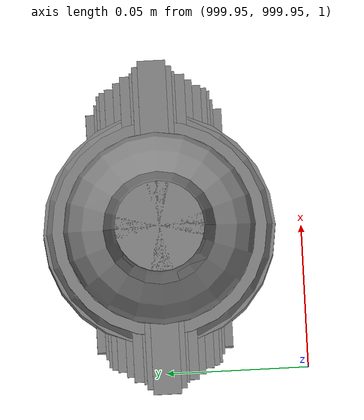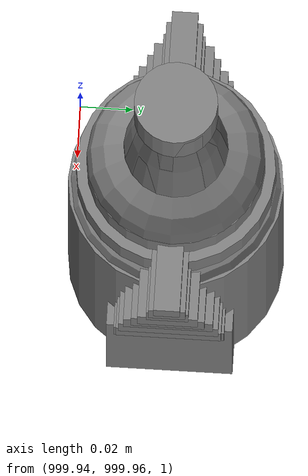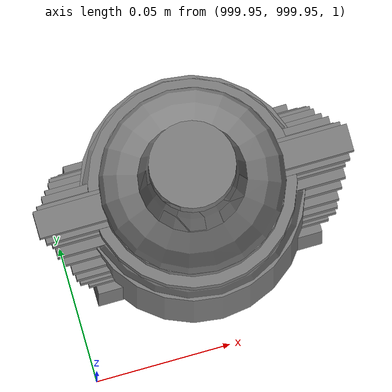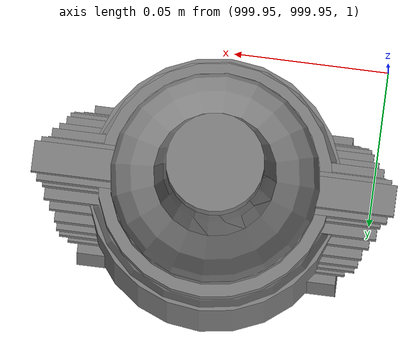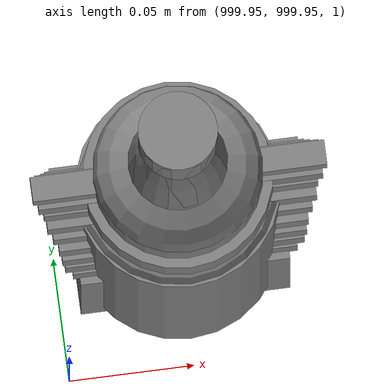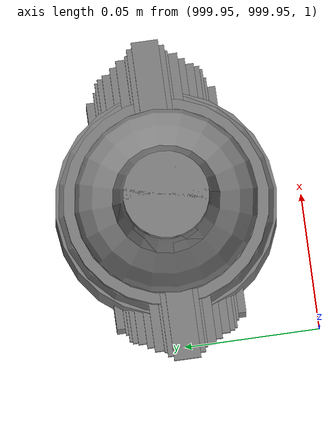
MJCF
<mujoco>
    <option gravity="0.000000000 0.000000000 -9.810000420" timestep="0.0166666" integrator="implicitfast" density="1.225" viscosity="1.8000001e-05" noslip_iterations="10" iterations="100" sdf_iterations="50">
        <flag multiccd="disable"/>
    </option>
    <size memory="1000M"/>
    <compiler coordinate="local"/>
    <worldbody>
        <light cutoff="30" pos="0 1 1" dir="0 -1 -2"/>
        <light cutoff="30" pos="0 -1 1" dir="0 1 -2"/>
        <body pos="0.000000000 0.000000000 0.000000000" euler="0.000000000 0.000000000 0.000000000" name="Interactive Objects_Interactive Objects"/>
        <body pos="-1.982940197 6.199763298 1.801599264" euler="-54.128520966 54.113212585 -129.848770142" mocap="true" name="spotlight3_SpotLight"/>
        <body pos="1000.000000000 1000.000000000 1.000000000" euler="0.000000000 0.000000000 0.000000000" name="openloong_gripper_2f85_fix_base_usda_can">
            <geom contype="1" conaffinity="1" density="1000" type="cylinder" material="" rgba="0.500000000 0.500000000 0.500000000 1.000000000" solimp="0.899999976 0.949999988 0.001000000" friction="1.000000000 0.005000000 0.000100000" solref="0.020000000 1.000000000" margin="0" condim="3" group="0" pos="0.000000000 0.000000000 0.079676986" quat="1.000000000 0.000000000 0.000000000 0.000000000" size="0.034000002 0.071999997 1.000000000" name="openloong_gripper_2f85_fix_base_usda_geom_39858311_2EAF_4E92_82D2_19C89E969BD8"/>
            <geom contype="1" conaffinity="1" density="1000" type="ellipsoid" material="" rgba="0.500000000 0.500000000 0.500000000 1.000000000" solimp="0.899999976 0.949999988 0.001000000" friction="1.000000000 0.005000000 0.000100000" solref="0.020000000 1.000000000" margin="0" condim="3" group="0" pos="0.000000000 0.000000000 0.151854277" quat="1.000000000 0.000000000 0.000000000 0.000000000" size="0.034000002 0.034000002 0.020000000" name="openloong_gripper_2f85_fix_base_usda_geom_18036FDC_15BA_47A4_8C24_6401AE65FACC"/>
            <geom contype="1" conaffinity="1" density="1000" type="box" material="" rgba="0.500000000 0.500000000 0.500000000 1.000000000" solimp="0.899999976 0.949999988 0.001000000" friction="1.000000000 0.005000000 0.000100000" solref="0.020000000 1.000000000" margin="0" condim="3" group="0" pos="0.000000000 0.000000000 0.004777670" quat="1.000000000 0.000000000 0.000000000 0.000000000" size="0.020000000 0.020000000 0.005000000" name="openloong_gripper_2f85_fix_base_usda_geom_C03830E0_70C3_4814_A2B7_E02B396E4669"/>
            <freejoint name="openloong_gripper_2f85_fix_base_usda_can_joint"/>
            <site size="0.005000000 0.005000000 0.005000000" rgba="0.500000000 0.500000000 0.500000000 1.000000000" pos="0.000000000 0.000000000 0.000000000" quat="1.000000000 0.000000000 0.000000000 0.000000000" group="0" type="sphere" name="openloong_gripper_2f85_fix_base_usda_cansite"/>
        </body>
        <body pos="1000.000000000 1000.000000000 1.000000000" euler="0.000000000 0.000000000 0.000000000" name="openloong_gripper_2f85_fix_base_usda_jar_01">
            <geom contype="1" conaffinity="1" density="1000" type="box" material="" rgba="0.500000000 0.500000000 0.500000000 1.000000000" solimp="0.899999976 0.949999988 0.001000000" friction="1.000000000 0.005000000 0.000100000" solref="0.020000000 1.000000000" margin="0" condim="3" group="0" pos="0.000000000 0.000000000 0.006158113" quat="1.000000000 0.000000000 0.000000000 0.000000000" size="0.020000000 0.020000000 0.005000000" name="openloong_gripper_2f85_fix_base_usda_geom_4953AE94_E781_4C96_9741_AB2755E26B71"/>
            <geom contype="1" conaffinity="1" density="1000" type="cylinder" material="" rgba="0.500000000 0.500000000 0.500000000 1.000000000" solimp="0.899999976 0.949999988 0.001000000" friction="1.000000000 0.005000000 0.000100000" solref="0.020000000 1.000000000" margin="0" condim="3" group="0" pos="0.000000000 0.000000000 0.062744498" quat="1.000000000 0.000000000 0.000000000 0.000000000" size="0.041000001 0.052999999 1.000000000" name="openloong_gripper_2f85_fix_base_usda_geom_5C55AF9B_09D6_448E_AD8D_015D6B41D003"/>
            <geom contype="1" conaffinity="1" density="1000" type="ellipsoid" material="" rgba="0.500000000 0.500000000 0.500000000 1.000000000" solimp="0.899999976 0.949999988 0.001000000" friction="1.000000000 0.005000000 0.000100000" solref="0.020000000 1.000000000" margin="0" condim="3" group="0" pos="0.000000000 0.000000000 0.122252703" quat="1.000000000 0.000000000 0.000000000 0.000000000" size="0.035999998 0.035999998 0.010000000" name="openloong_gripper_2f85_fix_base_usda_geom_6EF92BA3_D6BC_4919_AB89_E836A0A1806D"/>
            <geom contype="1" conaffinity="1" density="1000" type="cylinder" material="" rgba="0.500000000 0.500000000 0.500000000 1.000000000" solimp="0.899999976 0.949999988 0.001000000" friction="1.000000000 0.005000000 0.000100000" solref="0.020000000 1.000000000" margin="0" condim="3" group="0" pos="0.000000000 0.000000000 0.015747190" quat="1.000000000 0.000000000 0.000000000 0.000000000" size="0.035000000 0.010000000 1.000000000" name="openloong_gripper_2f85_fix_base_usda_geom_7619057C_3051_44C8_A8C3_26370F6FB78A"/>
            <geom contype="1" conaffinity="1" density="1000" type="ellipsoid" material="" rgba="0.500000000 0.500000000 0.500000000 1.000000000" solimp="0.899999976 0.949999988 0.001000000" friction="1.000000000 0.005000000 0.000100000" solref="0.020000000 1.000000000" margin="0" condim="3" group="0" pos="0.000000000 0.000000000 0.115815401" quat="1.000000000 0.000000000 0.000000000 0.000000000" size="0.039999999 0.039999999 0.010000000" name="openloong_gripper_2f85_fix_base_usda_geom_456D5A69_ABEC_485C_9F6F_EC90297D3CB3"/>
            <geom contype="1" conaffinity="1" density="1000" type="cylinder" material="" rgba="0.500000000 0.500000000 0.500000000 1.000000000" solimp="0.899999976 0.949999988 0.001000000" friction="1.000000000 0.005000000 0.000100000" solref="0.020000000 1.000000000" margin="0" condim="3" group="0" pos="0.000000000 0.000000000 0.133183479" quat="1.000000000 0.000000000 0.000000000 0.000000000" size="0.037999999 0.006500000 1.000000000" name="openloong_gripper_2f85_fix_base_usda_geom_F668DDE4_8FCC_44B2_BF99_62E3C45D922C"/>
            <freejoint name="openloong_gripper_2f85_fix_base_usda_jar_01_joint"/>
            <site size="0.005000000 0.005000000 0.005000000" rgba="0.500000000 0.500000000 0.500000000 1.000000000" pos="0.000000000 0.000000000 0.000000000" quat="1.000000000 0.000000000 0.000000000 0.000000000" group="0" type="sphere" name="openloong_gripper_2f85_fix_base_usda_jar_01site"/>
        </body>
        <body pos="-2.063071012 6.164028168 1.746783376" euler="139.028076172 29.019283295 -63.554107666" mocap="true" name="spotlight2_SpotLight"/>
        <body pos="1000.000000000 1000.000000000 1.000000000" euler="0.000000000 0.000000000 0.000000000" name="openloong_gripper_2f85_fix_base_usda_bottle_red">
            <geom contype="1" conaffinity="1" density="1000" type="ellipsoid" material="" rgba="0.500000000 0.500000000 0.500000000 1.000000000" solimp="0.899999976 0.949999988 0.001000000" friction="1.000000000 0.005000000 0.000100000" solref="0.020000000 1.000000000" margin="0" condim="3" group="0" pos="0.000000000 0.000000000 0.144284487" quat="1.000000000 0.000000000 0.000000000 0.000000000" size="0.021000000 0.021000000 0.079999998" name="openloong_gripper_2f85_fix_base_usda_geom_A991255D_103E_4240_984B_B3A1F8690A58"/>
            <geom contype="1" conaffinity="1" density="1000" type="cylinder" material="" rgba="0.500000000 0.500000000 0.500000000 1.000000000" solimp="0.899999976 0.949999988 0.001000000" friction="1.000000000 0.005000000 0.000100000" solref="0.020000000 1.000000000" margin="0" condim="3" group="0" pos="0.000000000 0.000000000 0.220618963" quat="1.000000000 0.000000000 0.000000000 0.000000000" size="0.016000001 0.010000000 1.000000000" name="openloong_gripper_2f85_fix_base_usda_geom_62C0E467_62A9_4F8F_A17E_5A609AF7FD72"/>
            <geom contype="1" conaffinity="1" density="1000" type="ellipsoid" material="" rgba="0.500000000 0.500000000 0.500000000 1.000000000" solimp="0.899999976 0.949999988 0.001000000" friction="1.000000000 0.005000000 0.000100000" solref="0.020000000 1.000000000" margin="0" condim="3" group="0" pos="0.000000000 0.000000000 0.118945479" quat="1.000000000 0.000000000 0.000000000 0.000000000" size="0.030999999 0.030999999 0.029999999" name="openloong_gripper_2f85_fix_base_usda_geom_F2394E74_5E0F_4004_9535_EE33BBA1E13A"/>
            <geom contype="1" conaffinity="1" density="1000" type="box" material="" rgba="0.500000000 0.500000000 0.500000000 1.000000000" solimp="0.899999976 0.949999988 0.001000000" friction="1.000000000 0.005000000 0.000100000" solref="0.020000000 1.000000000" margin="0" condim="3" group="0" pos="0.000000000 0.000000000 0.002189159" quat="1.000000000 0.000000000 0.000000000 0.000000000" size="0.020000000 0.020000000 0.003000000" name="openloong_gripper_2f85_fix_base_usda_geom_5D9F1D8B_991F_4DEA_815A_E0E80F854844"/>
            <geom contype="1" conaffinity="1" density="1000" type="cylinder" material="" rgba="0.500000000 0.500000000 0.500000000 1.000000000" solimp="0.899999976 0.949999988 0.001000000" friction="1.000000000 0.005000000 0.000100000" solref="0.020000000 1.000000000" margin="0" condim="3" group="0" pos="0.000000000 -0.000366211 0.060884237" quat="1.000000000 0.000000000 0.000000000 0.000000000" size="0.030999999 0.057999998 1.000000000" name="openloong_gripper_2f85_fix_base_usda_geom_510CDB8A_5F6B_4F7A_AA49_42A5E6897DE8"/>
            <freejoint name="openloong_gripper_2f85_fix_base_usda_bottle_red_joint"/>
            <site size="0.005000000 0.005000000 0.005000000" rgba="0.500000000 0.500000000 0.500000000 1.000000000" pos="0.000000000 0.000000000 0.000000000" quat="0.999961913 0.008726535 0.000000000 0.000000000" group="0" type="sphere" name="openloong_gripper_2f85_fix_base_usda_bottle_redsite"/>
        </body>
        <body pos="-1.768263698 6.587317944 1.844706059" euler="22.547880173 -82.900970459 -68.597709656" mocap="true" name="spotlight4_SpotLight"/>
        <body pos="1000.000000000 1000.000000000 1.000000000" euler="0.000000000 0.000000000 0.000000000" name="openloong_gripper_2f85_fix_base_usda_salt">
            <geom contype="1" conaffinity="1" density="1000" type="box" material="" rgba="0.500000000 0.500000000 0.500000000 1.000000000" solimp="0.899999976 0.949999988 0.001000000" friction="1.000000000 0.005000000 0.000100000" solref="0.020000000 1.000000000" margin="0" condim="3" group="0" pos="0.000305176 0.000000000 0.084862232" quat="1.000000000 0.000000000 0.000000000 0.000000000" size="0.048999999 0.018999999 0.005000000" name="openloong_gripper_2f85_fix_base_usda_geom_3928CDA9_279C_4035_8E49_300C62D04066"/>
            <geom contype="1" conaffinity="1" density="1000" type="box" material="" rgba="0.500000000 0.500000000 0.500000000 1.000000000" solimp="0.899999976 0.949999988 0.001000000" friction="1.000000000 0.005000000 0.000100000" solref="0.020000000 1.000000000" margin="0" condim="3" group="0" pos="0.000305176 0.000000000 0.104564309" quat="1.000000000 0.000000000 0.000000000 0.000000000" size="0.052000001 0.014000000 0.005000000" name="openloong_gripper_2f85_fix_base_usda_geom_06FF7506_2E33_49C3_A487_3F82213938FF"/>
            <geom contype="1" conaffinity="1" density="1000" type="box" material="" rgba="0.500000000 0.500000000 0.500000000 1.000000000" solimp="0.899999976 0.949999988 0.001000000" friction="1.000000000 0.005000000 0.000100000" solref="0.020000000 1.000000000" margin="0" condim="3" group="0" pos="0.000305176 0.000000000 0.114487171" quat="1.000000000 0.000000000 0.000000000 0.000000000" size="0.054000001 0.011500000 0.005000000" name="openloong_gripper_2f85_fix_base_usda_geom_E8A8F8A3_9B7D_40D1_B3F1_5FF3F953A2D2"/>
            <geom contype="1" conaffinity="1" density="1000" type="box" material="" rgba="0.500000000 0.500000000 0.500000000 1.000000000" solimp="0.899999976 0.949999988 0.001000000" friction="1.000000000 0.005000000 0.000100000" solref="0.020000000 1.000000000" margin="0" condim="3" group="0" pos="0.000305176 0.000000000 0.075103164" quat="1.000000000 0.000000000 0.000000000 0.000000000" size="0.048000000 0.020000000 0.005000000" name="openloong_gripper_2f85_fix_base_usda_geom_9BCF1594_4E85_4F26_B0BA_407F234FD57D"/>
            <geom contype="1" conaffinity="1" density="1000" type="box" material="" rgba="0.500000000 0.500000000 0.500000000 1.000000000" solimp="0.899999976 0.949999988 0.001000000" friction="1.000000000 0.005000000 0.000100000" solref="0.020000000 1.000000000" margin="0" condim="3" group="0" pos="0.000305176 0.000000000 0.134892464" quat="1.000000000 0.000000000 0.000000000 0.000000000" size="0.057000000 0.007000000 0.005000000" name="openloong_gripper_2f85_fix_base_usda_geom_9CD79FAA_6A9A_4A81_A807_5456624BC4EB"/>
            <geom contype="1" conaffinity="1" density="1000" type="box" material="" rgba="0.500000000 0.500000000 0.500000000 1.000000000" solimp="0.899999976 0.949999988 0.001000000" friction="1.000000000 0.005000000 0.000100000" solref="0.020000000 1.000000000" margin="0" condim="3" group="0" pos="0.000305176 0.000000000 0.094920278" quat="1.000000000 0.000000000 0.000000000 0.000000000" size="0.050000001 0.017000001 0.005000000" name="openloong_gripper_2f85_fix_base_usda_geom_71C8E3F0_B1FB_457C_BDD0_3DACCD6243BB"/>
            <geom contype="1" conaffinity="1" density="1000" type="box" material="" rgba="0.500000000 0.500000000 0.500000000 1.000000000" solimp="0.899999976 0.949999988 0.001000000" friction="1.000000000 0.005000000 0.000100000" solref="0.020000000 1.000000000" margin="0" condim="3" group="0" pos="0.000305176 0.000000000 0.065204859" quat="1.000000000 0.000000000 0.000000000 0.000000000" size="0.045000002 0.021000000 0.005000000" name="openloong_gripper_2f85_fix_base_usda_geom_0B9B0719_F8EE_4246_A5D7_88926A71295A"/>
            <geom contype="1" conaffinity="1" density="1000" type="box" material="" rgba="0.500000000 0.500000000 0.500000000 1.000000000" solimp="0.899999976 0.949999988 0.001000000" friction="1.000000000 0.005000000 0.000100000" solref="0.020000000 1.000000000" margin="0" condim="3" group="0" pos="0.000305176 0.000000000 0.144135714" quat="1.000000000 0.000000000 0.000000000 0.000000000" size="0.059000000 0.005000000 0.004000000" name="openloong_gripper_2f85_fix_base_usda_geom_6C3AE101_36B1_430B_AB0C_5AA0DF36EE94"/>
            <geom contype="1" conaffinity="1" density="1000" type="box" material="" rgba="0.500000000 0.500000000 0.500000000 1.000000000" solimp="0.899999976 0.949999988 0.001000000" friction="1.000000000 0.005000000 0.000100000" solref="0.020000000 1.000000000" margin="0" condim="3" group="0" pos="0.000000000 0.000000000 0.031593561" quat="1.000000000 0.000000000 0.000000000 0.000000000" size="0.041999999 0.024000000 0.029999999" name="openloong_gripper_2f85_fix_base_usda_geom_02D59D3F_D093_41C4_9157_B6D10DDFD63A"/>
            <geom contype="1" conaffinity="1" density="1000" type="box" material="" rgba="0.500000000 0.500000000 0.500000000 1.000000000" solimp="0.899999976 0.949999988 0.001000000" friction="1.000000000 0.005000000 0.000100000" solref="0.020000000 1.000000000" margin="0" condim="3" group="0" pos="0.000305176 0.000000000 0.124608755" quat="1.000000000 0.000000000 0.000000000 0.000000000" size="0.055000000 0.008000000 0.005000000" name="openloong_gripper_2f85_fix_base_usda_geom_8F0E3742_9843_4ABA_9D6C_6DB269F33E16"/>
            <freejoint name="openloong_gripper_2f85_fix_base_usda_salt_joint"/>
            <site size="0.005000000 0.005000000 0.005000000" rgba="0.500000000 0.500000000 0.500000000 1.000000000" pos="0.000000000 0.000000000 0.000000000" quat="1.000000000 0.000000000 0.000000000 0.000000000" group="0" type="sphere" name="openloong_gripper_2f85_fix_base_usda_saltsite"/>
        </body>
        <body pos="1000.000000000 1000.000000000 1.000000000" euler="0.000000000 0.000000000 0.000000000" name="openloong_gripper_2f85_fix_base_usda_bottle_blue">
            <geom contype="1" conaffinity="1" density="1000" type="ellipsoid" material="" rgba="0.500000000 0.500000000 0.500000000 1.000000000" solimp="0.899999976 0.949999988 0.001000000" friction="1.000000000 0.005000000 0.000100000" solref="0.020000000 1.000000000" margin="0" condim="3" group="0" pos="0.000000000 0.000000000 0.118920922" quat="1.000000000 0.000000000 0.000000000 0.000000000" size="0.030999999 0.030999999 0.029999999" name="openloong_gripper_2f85_fix_base_usda_geom_8B91608D_1238_4F46_97F8_9E6CD7E0FE57"/>
            <geom contype="1" conaffinity="1" density="1000" type="box" material="" rgba="0.500000000 0.500000000 0.500000000 1.000000000" solimp="0.899999976 0.949999988 0.001000000" friction="1.000000000 0.005000000 0.000100000" solref="0.020000000 1.000000000" margin="0" condim="3" group="0" pos="0.000000000 0.000000000 0.002164602" quat="1.000000000 0.000000000 0.000000000 0.000000000" size="0.020000000 0.020000000 0.003000000" name="openloong_gripper_2f85_fix_base_usda_geom_9BFD3647_E7A7_4B64_B2B5_E58D85E12043"/>
            <geom contype="1" conaffinity="1" density="1000" type="cylinder" material="" rgba="0.500000000 0.500000000 0.500000000 1.000000000" solimp="0.899999976 0.949999988 0.001000000" friction="1.000000000 0.005000000 0.000100000" solref="0.020000000 1.000000000" margin="0" condim="3" group="0" pos="0.000000000 -0.000366211 0.060859680" quat="1.000000000 0.000000000 0.000000000 0.000000000" size="0.030999999 0.057999998 1.000000000" name="openloong_gripper_2f85_fix_base_usda_geom_3DEFC91F_99B7_471C_92A6_8BFF8C6CCDCB"/>
            <geom contype="1" conaffinity="1" density="1000" type="cylinder" material="" rgba="0.500000000 0.500000000 0.500000000 1.000000000" solimp="0.899999976 0.949999988 0.001000000" friction="1.000000000 0.005000000 0.000100000" solref="0.020000000 1.000000000" margin="0" condim="3" group="0" pos="0.000000000 0.000000000 0.220594406" quat="1.000000000 0.000000000 0.000000000 0.000000000" size="0.016000001 0.010000000 1.000000000" name="openloong_gripper_2f85_fix_base_usda_geom_41F63C0C_F925_4D0C_9F80_C0174C140BC9"/>
            <geom contype="1" conaffinity="1" density="1000" type="ellipsoid" material="" rgba="0.500000000 0.500000000 0.500000000 1.000000000" solimp="0.899999976 0.949999988 0.001000000" friction="1.000000000 0.005000000 0.000100000" solref="0.020000000 1.000000000" margin="0" condim="3" group="0" pos="0.000000000 0.000000000 0.144259930" quat="1.000000000 0.000000000 0.000000000 0.000000000" size="0.021000000 0.021000000 0.079999998" name="openloong_gripper_2f85_fix_base_usda_geom_9CE25DB6_FE8C_445A_BC47_8A4F9E0D0DE0"/>
            <freejoint name="openloong_gripper_2f85_fix_base_usda_bottle_blue_joint"/>
            <site size="0.005000000 0.005000000 0.005000000" rgba="0.500000000 0.500000000 0.500000000 1.000000000" pos="0.000000000 0.000000000 0.000000000" quat="0.999961913 0.008726535 0.000000000 0.000000000" group="0" type="sphere" name="openloong_gripper_2f85_fix_base_usda_bottle_bluesite"/>
        </body>
        <body pos="0.000000000 0.000000000 0.000000000" euler="0.000000000 0.000000000 0.000000000" name=" Static Objects_ Static Objects">
            <geom contype="1" conaffinity="1" density="1000" type="box" material="" rgba="0.500000000 0.500000000 0.500000000 1.000000000" solimp="0.899999976 0.949999988 0.001000000" friction="1.000000000 0.005000000 0.000100000" solref="0.020000000 1.000000000" margin="0" condim="3" group="0" pos="-3.101639986 6.150595188 1.018643856" quat="1.000000000 0.000000000 0.000000000 0.000000000" size="0.050000001 0.579999983 1.019999981" name=" Static Objects_geom_7CE54535_C3C5_4967_9FEE_99770644ADD4"/>
            <geom contype="1" conaffinity="1" density="1000" type="box" material="" rgba="0.500000000 0.500000000 0.500000000 1.000000000" solimp="0.899999976 0.949999988 0.001000000" friction="1.000000000 0.005000000 0.000100000" solref="0.020000000 1.000000000" margin="0" condim="3" group="0" pos="-2.825197220 6.153595448 1.115278244" quat="0.707107067 0.000000000 0.000000000 0.707106471" size="0.550000012 0.239999995 0.025000000" name=" Static Objects_geom_6A7D05A5_3B6D_44CC_BCC9_0EF4552AADC7"/>
            <geom contype="1" conaffinity="1" density="1000" type="box" material="" rgba="0.500000000 0.500000000 0.500000000 1.000000000" solimp="0.899999976 0.949999988 0.001000000" friction="1.000000000 0.005000000 0.000100000" solref="0.020000000 1.000000000" margin="0" condim="3" group="0" pos="-2.825197220 6.153595448 0.097434282" quat="0.707107067 0.000000000 0.000000000 0.707106471" size="0.550000012 0.239999995 0.098999999" name=" Static Objects_geom_E05320BA_E29E_4D9A_A149_25DA3F97F5DA"/>
            <geom contype="1" conaffinity="1" density="1000" type="box" material="" rgba="0.500000000 0.500000000 0.500000000 1.000000000" solimp="0.899999976 0.949999988 0.001000000" friction="1.000000000 0.005000000 0.000100000" solref="0.020000000 1.000000000" margin="0" condim="3" group="0" pos="-6.293097973 6.153595448 1.114443064" quat="0.707107067 0.000000000 0.000000000 0.707106471" size="0.529999971 3.134999990 0.025000000" name=" Static Objects_geom_45CB2966_D41F_4C7D_8F69_705E47ACF57A"/>
            <geom contype="1" conaffinity="1" density="1000" type="box" material="" rgba="0.500000000 0.500000000 0.500000000 1.000000000" solimp="0.899999976 0.949999988 0.001000000" friction="1.000000000 0.005000000 0.000100000" solref="0.020000000 1.000000000" margin="0" condim="3" group="0" pos="-6.286010742 6.153595448 0.096129179" quat="0.707107067 0.000000000 0.000000000 0.707106471" size="0.529999971 3.134999990 0.098999999" name=" Static Objects_geom_7659CDC1_D532_4630_8C24_5E2679F9ADD4"/>
            <geom contype="1" conaffinity="1" density="1000" type="box" material="" rgba="0.500000000 0.500000000 0.500000000 1.000000000" solimp="0.899999976 0.949999988 0.001000000" friction="1.000000000 0.005000000 0.000100000" solref="0.020000000 1.000000000" margin="0" condim="3" group="0" pos="-2.825197220 6.153595448 1.563861728" quat="0.707107067 0.000000000 0.000000000 0.707106471" size="0.550000012 0.239999995 0.025000000" name=" Static Objects_geom_96BC7205_B123_45ED_9DB8_5425107AFC33"/>
            <geom contype="1" conaffinity="1" density="1000" type="box" material="" rgba="0.500000000 0.500000000 0.500000000 1.000000000" solimp="0.899999976 0.949999988 0.001000000" friction="1.000000000 0.005000000 0.000100000" solref="0.020000000 1.000000000" margin="0" condim="3" group="0" pos="-6.311686516 6.153595448 1.018643856" quat="0.707107067 0.000000000 0.000000000 0.707106471" size="0.050000001 3.150000095 1.019999981" name=" Static Objects_geom_A9BF7E1F_55E9_4785_A0FA_CE86A8395577"/>
            <geom contype="1" conaffinity="1" density="1000" type="box" material="" rgba="0.500000000 0.500000000 0.500000000 1.000000000" solimp="0.899999976 0.949999988 0.001000000" friction="1.000000000 0.005000000 0.000100000" solref="0.020000000 1.000000000" margin="0" condim="3" group="0" pos="-2.825197220 6.153595448 0.629031777" quat="0.707107067 0.000000000 0.000000000 0.707106471" size="0.550000012 0.239999995 0.025000000" name=" Static Objects_geom_C4CEA2D6_F073_4CC1_9409_81423D891A72"/>
            <geom contype="1" conaffinity="1" density="1000" type="box" material="" rgba="0.500000000 0.500000000 0.500000000 1.000000000" solimp="0.899999976 0.949999988 0.001000000" friction="1.000000000 0.005000000 0.000100000" solref="0.020000000 1.000000000" margin="0" condim="3" group="0" pos="-6.286010742 6.153595448 1.563861728" quat="0.707107067 0.000000000 0.000000000 0.707106471" size="0.529999971 3.134999990 0.025000000" name=" Static Objects_geom_B71FB7A0_665D_46F4_B6D1_7376BCC662EA"/>
            <geom contype="1" conaffinity="1" density="1000" type="box" material="" rgba="0.500000000 0.500000000 0.500000000 1.000000000" solimp="0.899999976 0.949999988 0.001000000" friction="1.000000000 0.005000000 0.000100000" solref="0.020000000 1.000000000" margin="0" condim="3" group="0" pos="-6.286010742 6.153595448 0.629031777" quat="0.707107067 0.000000000 0.000000000 0.707106471" size="0.529999971 3.134999990 0.025000000" name=" Static Objects_geom_5797B0A7_F703_4F61_A224_0744360186EC"/>
            <geom contype="1" conaffinity="1" density="1000" type="box" material="" rgba="0.500000000 0.500000000 0.500000000 1.000000000" solimp="0.899999976 0.949999988 0.001000000" friction="1.000000000 0.005000000 0.000100000" solref="0.020000000 1.000000000" margin="0" condim="3" group="0" pos="-7.719123363 2.867671013 1.173410416" quat="1.000000000 0.000000000 0.000000000 0.000000000" size="0.250000000 0.250000000 0.079999998" name=" Static Objects_geom_D09C33FE_D293_4533_A982_042A7258BAE0"/>
            <geom contype="1" conaffinity="1" density="1000" type="box" material="" rgba="0.500000000 0.500000000 0.500000000 1.000000000" solimp="0.899999976 0.949999988 0.001000000" friction="1.000000000 0.005000000 0.000100000" solref="0.020000000 1.000000000" margin="0" condim="3" group="0" pos="-7.408766270 3.088089943 1.776644945" quat="0.928051054 0.000000000 0.000000000 0.372453064" size="0.050000001 0.100000001 0.050000001" name=" Static Objects_geom_4AB12149_4810_4B08_BC82_0432E3189B94"/>
            <geom contype="1" conaffinity="1" density="1000" type="box" material="" rgba="0.500000000 0.500000000 0.500000000 1.000000000" solimp="0.899999976 0.949999988 0.001000000" friction="1.000000000 0.005000000 0.000100000" solref="0.020000000 1.000000000" margin="0" condim="3" group="0" pos="-7.719123363 2.958004713 1.530241251" quat="1.000000000 0.000000000 0.000000000 0.000000000" size="0.250000000 0.159999996 0.280000001" name=" Static Objects_geom_AC617592_A6A3_4459_881A_B51A931B9C02"/>
            <geom contype="1" conaffinity="1" density="1000" type="cylinder" material="" rgba="0.500000000 0.500000000 0.500000000 1.000000000" solimp="0.899999976 0.949999988 0.001000000" friction="1.000000000 0.005000000 0.000100000" solref="0.020000000 1.000000000" margin="0" condim="3" group="0" pos="-7.427312374 3.069516420 1.502544641" quat="0.928051054 0.000000000 0.000000000 0.372453064" size="0.015000000 0.230000004 0.100000001" name=" Static Objects_geom_5AF05451_A75E_4594_ADE5_D2B69A8DD152"/>
            <geom contype="1" conaffinity="1" density="1000" type="box" material="" rgba="0.500000000 0.500000000 0.500000000 1.000000000" solimp="0.899999976 0.949999988 0.001000000" friction="1.000000000 0.005000000 0.000100000" solref="0.020000000 1.000000000" margin="0" condim="3" group="0" pos="-7.437745571 3.067511320 1.289965630" quat="1.000000000 0.000000000 0.000000000 0.000000000" size="0.029999999 0.020000000 0.020000000" name=" Static Objects_geom_8EB119C2_06D7_4E46_951D_1BD63E367607"/>
            <geom contype="1" conaffinity="1" density="1000" type="box" material="" rgba="0.500000000 0.500000000 0.500000000 1.000000000" solimp="0.899999976 0.949999988 0.001000000" friction="1.000000000 0.005000000 0.000100000" solref="0.020000000 1.000000000" margin="0" condim="3" group="0" pos="-9.058088303 6.434794426 1.209077358" quat="1.000000000 0.000000000 0.000000000 0.000000000" size="0.250000000 0.100000001 0.070000000" name=" Static Objects_geom_2717FFCF_2B65_4869_A787_1A9CCDA75658"/>
            <geom contype="1" conaffinity="1" density="1000" type="box" material="" rgba="0.500000000 0.500000000 0.500000000 1.000000000" solimp="0.899999976 0.949999988 0.001000000" friction="1.000000000 0.005000000 0.000100000" solref="0.020000000 1.000000000" margin="0" condim="3" group="0" pos="-7.886891365 6.459744930 0.352518857" quat="1.000000000 0.000000000 0.000000000 0.000000000" size="1.500000000 0.200000003 0.150000006" name=" Static Objects_geom_3F5E0EFD_0BFB_464B_B061_0A5756060448"/>
            <geom contype="1" conaffinity="1" density="1000" type="box" material="" rgba="0.500000000 0.500000000 0.500000000 1.000000000" solimp="0.899999976 0.949999988 0.001000000" friction="1.000000000 0.005000000 0.000100000" solref="0.020000000 1.000000000" margin="0" condim="3" group="0" pos="-9.237723351 6.464855671 1.209077358" quat="1.000000000 0.000000000 0.000000000 0.000000000" size="0.100000001 0.100000001 0.070000000" name=" Static Objects_geom_734192E6_CD1E_4215_9D55_33C08114DBB0"/>
            <geom contype="1" conaffinity="1" density="1000" type="box" material="" rgba="0.500000000 0.500000000 0.500000000 1.000000000" solimp="0.899999976 0.949999988 0.001000000" friction="1.000000000 0.005000000 0.000100000" solref="0.020000000 1.000000000" margin="0" condim="3" group="0" pos="-6.924745083 6.362090111 1.214329123" quat="1.000000000 0.000000000 0.000000000 0.000000000" size="0.200000003 0.100000001 0.075000003" name=" Static Objects_geom_34C0CE90_8C6D_4FAB_B4AA_AAE76C9EC0AB"/>
            <geom contype="1" conaffinity="1" density="1000" type="box" material="" rgba="0.500000000 0.500000000 0.500000000 1.000000000" solimp="0.899999976 0.949999988 0.001000000" friction="1.000000000 0.005000000 0.000100000" solref="0.020000000 1.000000000" margin="0" condim="3" group="0" pos="-4.407354832 6.459744930 1.292199373" quat="1.000000000 0.000000000 0.000000000 0.000000000" size="1.240000010 0.200000003 0.150000006" name=" Static Objects_geom_DA95F9BE_6C71_4320_81D7_C790002B632C"/>
            <geom contype="1" conaffinity="1" density="1000" type="box" material="" rgba="0.500000000 0.500000000 0.500000000 1.000000000" solimp="0.899999976 0.949999988 0.001000000" friction="1.000000000 0.005000000 0.000100000" solref="0.020000000 1.000000000" margin="0" condim="3" group="0" pos="-5.611940861 6.318420410 0.350975692" quat="1.000000000 0.000000000 0.000000000 0.000000000" size="0.699999988 0.100000001 0.150000006" name=" Static Objects_geom_6CC4B953_D3A8_4DBF_8A7B_8AA663335072"/>
            <geom contype="1" conaffinity="1" density="1000" type="box" material="" rgba="0.500000000 0.500000000 0.500000000 1.000000000" solimp="0.899999976 0.949999988 0.001000000" friction="1.000000000 0.005000000 0.000100000" solref="0.020000000 1.000000000" margin="0" condim="3" group="0" pos="-6.300771236 6.459744930 1.744376063" quat="1.000000000 0.000000000 0.000000000 0.000000000" size="3.000000000 0.200000003 0.150000006" name=" Static Objects_geom_A1F5C744_FED4_4711_8100_6DA507142F88"/>
            <geom contype="1" conaffinity="1" density="1000" type="box" material="" rgba="0.500000000 0.500000000 0.500000000 1.000000000" solimp="0.899999976 0.949999988 0.001000000" friction="1.000000000 0.005000000 0.000100000" solref="0.020000000 1.000000000" margin="0" condim="3" group="0" pos="-6.751636982 6.459744930 0.800981164" quat="1.000000000 0.000000000 0.000000000 0.000000000" size="2.200000048 0.200000003 0.150000006" name=" Static Objects_geom_5750CA2A_82C1_44ED_A188_7EA2FC0C26F5"/>
            <geom contype="1" conaffinity="1" density="1000" type="box" material="" rgba="0.500000000 0.500000000 0.500000000 1.000000000" solimp="0.899999976 0.949999988 0.001000000" friction="1.000000000 0.005000000 0.000100000" solref="0.020000000 1.000000000" margin="0" condim="3" group="0" pos="-8.844120979 6.464855671 1.209077358" quat="1.000000000 0.000000000 0.000000000 0.000000000" size="0.100000001 0.100000001 0.070000000" name=" Static Objects_geom_6E577DF5_203D_4625_B6A5_BB756D93DB88"/>
            <geom contype="1" conaffinity="1" density="1000" type="box" material="" rgba="0.500000000 0.500000000 0.500000000 1.000000000" solimp="0.899999976 0.949999988 0.001000000" friction="1.000000000 0.005000000 0.000100000" solref="0.020000000 1.000000000" margin="0" condim="3" group="0" pos="-6.098561764 6.327973843 1.292199373" quat="1.000000000 0.000000000 0.000000000 0.000000000" size="0.500000000 0.100000001 0.150000006" name=" Static Objects_geom_A1FD4E3A_8FFD_487D_9088_D9D317D1417F"/>
            <geom contype="1" conaffinity="1" density="1000" type="box" material="" rgba="0.500000000 0.500000000 0.500000000 1.000000000" solimp="0.899999976 0.949999988 0.001000000" friction="1.000000000 0.005000000 0.000100000" solref="0.020000000 1.000000000" margin="0" condim="3" group="0" pos="-6.824534416 6.447464466 1.212718010" quat="1.000000000 0.000000000 0.000000000 0.000000000" size="0.100000001 0.100000001 0.075000003" name=" Static Objects_geom_B7A81697_5168_48A1_A64D_6C87F8F68AF5"/>
            <geom contype="1" conaffinity="1" density="1000" type="box" material="" rgba="0.500000000 0.500000000 0.500000000 1.000000000" solimp="0.899999976 0.949999988 0.001000000" friction="1.000000000 0.005000000 0.000100000" solref="0.020000000 1.000000000" margin="0" condim="3" group="0" pos="-3.907610416 6.318625927 0.800981164" quat="1.000000000 0.000000000 0.000000000 0.000000000" size="0.500000000 0.100000001 0.150000006" name=" Static Objects_geom_EE6B3731_0F12_481A_AE8B_6C3D394D3B05"/>
            <geom contype="1" conaffinity="1" density="1000" type="box" material="" rgba="0.500000000 0.500000000 0.500000000 1.000000000" solimp="0.899999976 0.949999988 0.001000000" friction="1.000000000 0.005000000 0.000100000" solref="0.020000000 1.000000000" margin="0" condim="3" group="0" pos="-7.373087406 6.458900928 1.214329123" quat="1.000000000 0.000000000 0.000000000 0.000000000" size="0.250000000 0.200000003 0.075000003" name=" Static Objects_geom_308BC0E7_5FB6_498F_A4EE_CEA95D995B79"/>
            <geom contype="1" conaffinity="1" density="1000" type="box" material="" rgba="0.500000000 0.500000000 0.500000000 1.000000000" solimp="0.899999976 0.949999988 0.001000000" friction="1.000000000 0.005000000 0.000100000" solref="0.020000000 1.000000000" margin="0" condim="3" group="0" pos="-4.035642624 6.459744930 0.352518857" quat="1.000000000 0.000000000 0.000000000 0.000000000" size="0.800000012 0.200000003 0.150000006" name=" Static Objects_geom_DA70C9A6_A7DD_4F9B_B245_54D74C26F915"/>
            <geom contype="1" conaffinity="1" density="1000" type="box" material="" rgba="0.500000000 0.500000000 0.500000000 1.000000000" solimp="0.899999976 0.949999988 0.001000000" friction="1.000000000 0.005000000 0.000100000" solref="0.020000000 1.000000000" margin="0" condim="3" group="0" pos="-6.460197449 2.937205315 0.548931718" quat="1.000000000 0.000000000 0.000000000 0.000000000" size="2.650000095 0.430000007 0.550000012" name=" Static Objects_geom_1B84406E_8AA1_4C3E_A5CB_00BCB0B11A02"/>
            <geom contype="1" conaffinity="1" density="1000" type="box" material="" rgba="0.500000000 0.500000000 0.500000000 1.000000000" solimp="0.899999976 0.949999988 0.001000000" friction="1.000000000 0.005000000 0.000100000" solref="0.020000000 1.000000000" margin="0" condim="3" group="0" pos="-4.240264893 1.327049494 0.549888909" quat="1.000000000 0.000000000 0.000000000 0.000000000" size="0.430000007 1.200000048 0.550000012" name=" Static Objects_geom_CEFA1063_4A1A_4CA6_9D92_C5F9D6018E3D"/>
            <geom contype="1" conaffinity="1" density="1000" type="box" material="" rgba="0.500000000 0.500000000 0.500000000 1.000000000" solimp="0.899999976 0.949999988 0.001000000" friction="1.000000000 0.005000000 0.000100000" solref="0.020000000 1.000000000" margin="0" condim="3" group="0" pos="-8.830721855 2.096410990 0.549305558" quat="1.000000000 0.000000000 0.000000000 0.000000000" size="0.280000001 0.430000007 0.550000012" name=" Static Objects_geom_B8FC72D8_AE13_4CAE_9B4A_BB5FD28AE74A"/>
            <geom contype="1" conaffinity="1" density="1000" type="plane" material="" rgba="0.500000000 0.500000000 0.500000000 1.000000000" solimp="0.899999976 0.949999988 0.001000000" friction="1.000000000 0.005000000 0.000100000" solref="0.020000000 1.000000000" margin="0" condim="3" group="0" pos="-6.000000000 10.399999619 0.000000000" quat="1.000000000 0.000000000 0.000000000 0.000000000" size="6.050000191 10.800000191 0.010000000" name=" Static Objects_geom_EBB326A7_D931_42AE_B70F_58911C6E36A5"/>
            <geom contype="1" conaffinity="1" density="1000" type="box" material="" rgba="0.500000000 0.500000000 0.500000000 1.000000000" solimp="0.899999976 0.949999988 0.001000000" friction="1.000000000 0.005000000 0.000100000" solref="0.020000000 1.000000000" margin="0" condim="3" group="0" pos="-6.000000000 0.035000000 2.000000000" quat="1.000000000 0.000000000 0.000000000 0.000000000" size="6.079999924 0.070000000 2.000000000" name=" Static Objects_geom_ED874B53_FF93_4B24_BC8A_E85B7ACB2524"/>
            <geom contype="1" conaffinity="1" density="1000" type="box" material="" rgba="0.500000000 0.500000000 0.500000000 1.000000000" solimp="0.899999976 0.949999988 0.001000000" friction="1.000000000 0.005000000 0.000100000" solref="0.020000000 1.000000000" margin="0" condim="3" group="0" pos="-6.000000000 20.159999847 2.000000000" quat="1.000000000 0.000000000 0.000000000 0.000000000" size="6.079999924 0.070000000 2.000000000" name=" Static Objects_geom_13604C9B_813A_46FA_8B7D_0D9A46EEF785"/>
            <geom contype="1" conaffinity="1" density="1000" type="box" material="" rgba="0.500000000 0.500000000 0.500000000 1.000000000" solimp="0.899999976 0.949999988 0.001000000" friction="1.000000000 0.005000000 0.000100000" solref="0.020000000 1.000000000" margin="0" condim="3" group="0" pos="0.000000000 10.000000000 2.000000000" quat="1.000000000 0.000000000 0.000000000 0.000000000" size="0.070000000 10.500000000 2.000000000" name=" Static Objects_geom_97EAAC7E_D4EE_459A_A3DA_4E8B62643D54"/>
            <geom contype="1" conaffinity="1" density="1000" type="box" material="" rgba="0.500000000 0.500000000 0.500000000 1.000000000" solimp="0.899999976 0.949999988 0.001000000" friction="1.000000000 0.005000000 0.000100000" solref="0.020000000 1.000000000" margin="0" condim="3" group="0" pos="-12.050000191 10.000000000 2.000000000" quat="1.000000000 0.000000000 0.000000000 0.000000000" size="0.070000000 10.500000000 2.000000000" name=" Static Objects_geom_C376DA03_6F32_4299_B58F_E241D71B5375"/>
        </body>
        <body pos="-3.510578632 3.403555870 -0.000000100" euler="0.000000000 0.000000000 40.200675964" name="openloong_gripper_2f85_fix_base_usda_PZ">
            <geom contype="1" conaffinity="1" density="1000" type="box" material="" rgba="0.500000000 0.500000000 0.500000000 1.000000000" solimp="0.899999976 0.949999988 0.001000000" friction="1.000000000 0.005000000 0.000100000" solref="0.020000000 1.000000000" margin="0" condim="3" group="0" pos="-0.047453165 0.056484699 0.373715430" quat="0.934750080 0.077914521 0.028795123 0.345459938" size="0.180000007 0.010000000 0.379999995" name="openloong_gripper_2f85_fix_base_usda_geom_2C1DAECE_0226_41F6_BAFC_4DA638BEF0C4"/>
            <geom contype="1" conaffinity="1" density="1000" type="box" material="" rgba="0.500000000 0.500000000 0.500000000 1.000000000" solimp="0.899999976 0.949999988 0.001000000" friction="1.000000000 0.005000000 0.000100000" solref="0.020000000 1.000000000" margin="0" condim="3" group="0" pos="0.047452450 -0.054376602 0.374072611" quat="0.934387863 -0.082143910 -0.030358355 0.345326364" size="0.180000007 0.010000000 0.379999995" name="openloong_gripper_2f85_fix_base_usda_geom_B6B698E7_9C30_4007_ABBF_1DB55EC0481C"/>
            <freejoint name="openloong_gripper_2f85_fix_base_usda_PZ"/>
        </body>
        <body pos="-6.332345009 2.779978037 1.034067392" euler="0.000000000 0.000000000 0.000000000" name="openloong_gripper_2f85_fix_base_usda_basket">
            <geom contype="1" conaffinity="1" density="100000" type="box" material="" rgba="0.500000000 0.500000000 0.500000000 1.000000000" solimp="0.899999976 0.949999988 0.001000000" friction="1.000000000 0.899999976 0.000100000" solref="0.020000000 1.000000000" margin="0" condim="3" group="0" pos="-0.172339439 0.000000000 0.168361664" quat="0.706172407 -0.036353018 -0.036353093 0.706170976" size="0.200000003 0.006000000 0.108000003" name="openloong_gripper_2f85_fix_base_usda_geom_11686D76_42EC_458E_B8F3_B6E091982159"/>
            <geom contype="1" conaffinity="1" density="100000" type="box" material="" rgba="0.500000000 0.500000000 0.500000000 1.000000000" solimp="0.899999976 0.949999988 0.001000000" friction="1.000000000 0.899999976 0.000100000" solref="0.020000000 1.000000000" margin="0" condim="3" group="0" pos="-0.039724827 -0.188568115 0.167089701" quat="0.997537494 0.070135131 0.000000000 0.000000000" size="0.150000006 0.006000000 0.108000003" name="openloong_gripper_2f85_fix_base_usda_geom_55C2FD83_633C_4856_AFD2_442BB306C09B"/>
            <geom contype="1" conaffinity="1" density="100000" type="box" material="" rgba="0.500000000 0.500000000 0.500000000 1.000000000" solimp="0.899999976 0.949999988 0.001000000" friction="1.000000000 0.899999976 0.000100000" solref="0.020000000 1.000000000" margin="0" condim="3" group="0" pos="-0.039724827 0.188377380 0.167089701" quat="0.997489929 -0.070808925 0.000000000 0.000000000" size="0.150000006 0.006000000 0.108000003" name="openloong_gripper_2f85_fix_base_usda_geom_EAECEECC_CE2B_4453_A44B_09F8E913DFAD"/>
            <geom contype="1" conaffinity="1" density="100000" type="box" material="" rgba="0.500000000 0.500000000 0.500000000 1.000000000" solimp="0.899999976 0.949999988 0.001000000" friction="1.000000000 0.899999976 0.000100000" solref="0.020000000 1.000000000" margin="0" condim="3" group="0" pos="-0.039724827 0.000000000 0.068126202" quat="1.000000000 0.000000000 0.000000000 0.000000000" size="0.129999995 0.174999997 0.006000000" name="openloong_gripper_2f85_fix_base_usda_geom_EBB2E317_A26F_435B_ADAE_15EC00E65E79"/>
            <geom contype="1" conaffinity="1" density="100000" type="box" material="" rgba="0.500000000 0.500000000 0.500000000 1.000000000" solimp="0.899999976 0.949999988 0.001000000" friction="1.000000000 0.899999976 0.000100000" solref="0.020000000 1.000000000" margin="0" condim="3" group="0" pos="0.094372749 0.000000000 0.168361664" quat="0.706172049 0.036353335 0.036353379 0.706171215" size="0.200000003 0.006000000 0.108000003" name="openloong_gripper_2f85_fix_base_usda_geom_2CAEF04A_4DA9_4326_90DF_E4F57604AF5A"/>
            <freejoint name="openloong_gripper_2f85_fix_base_usda_basket_joint"/>
            <site size="0.005000000 0.005000000 0.005000000" rgba="0.500000000 0.500000000 0.500000000 1.000000000" pos="0.000000000 0.000000000 0.000000000" quat="1.000000000 0.000000000 0.000000000 0.000000000" group="0" type="sphere" name="openloong_gripper_2f85_fix_base_usda_basketsite"/>
        </body>
        <body pos="-2.436573029 6.404376507 0.137849092" euler="0.000000000 0.000000000 0.000000000" name="openloong_gripper_2f85_fix_base_usda_shoppingtrolley_01">
            <geom contype="1" conaffinity="1" density="1000" type="box" material="" rgba="0.500000000 0.500000000 0.500000000 1.000000000" solimp="0.899999976 0.949999988 0.001000000" friction="1.000000000 0.005000000 0.000100000" solref="0.020000000 1.000000000" margin="0" condim="3" group="0" pos="-0.169898406 -0.178061336 0.864131629" quat="0.916343808 -0.400392294 -0.000000045 0.000000030" size="0.017999999 0.022499999 0.089999996" name="openloong_gripper_2f85_fix_base_usda_geom_DBB7B621_945F_4B7F_8060_11BAC290957C"/>
            <geom contype="1" conaffinity="1" density="1000" type="box" material="" rgba="0.500000000 0.500000000 0.500000000 1.000000000" solimp="0.899999976 0.949999988 0.001000000" friction="1.000000000 0.005000000 0.000100000" solref="0.020000000 1.000000000" margin="0" condim="3" group="0" pos="-0.107458733 0.238907143 0.911498845" quat="0.634576976 0.622505128 -0.330067992 -0.317575932" size="0.017999999 0.022499999 0.035999998" name="openloong_gripper_2f85_fix_base_usda_geom_AB00434E_072B_4BAA_905D_26BCAE2D44C1"/>
            <geom contype="1" conaffinity="1" density="1000" type="box" material="" rgba="0.500000000 0.500000000 0.500000000 1.000000000" solimp="0.899999976 0.949999988 0.001000000" friction="1.000000000 0.005000000 0.000100000" solref="0.020000000 1.000000000" margin="0" condim="3" group="0" pos="-0.005004787 0.248085022 0.912686050" quat="1.000000000 0.000000000 0.000000000 0.000000000" size="0.107999995 0.022499999 0.022499999" name="openloong_gripper_2f85_fix_base_usda_geom_D93F9B4F_D79E_4FAD_90DB_9954BC8E8D1C"/>
            <geom contype="1" conaffinity="1" density="1000" type="box" material="" rgba="0.500000000 0.500000000 0.500000000 1.000000000" solimp="0.899999976 0.949999988 0.001000000" friction="1.000000000 0.005000000 0.000100000" solref="0.020000000 1.000000000" margin="0" condim="3" group="0" pos="0.131482959 -0.182533979 0.598989725" quat="0.996607125 0.055331629 0.059003670 0.015205893" size="0.013499999 0.287999988 0.053999998" name="openloong_gripper_2f85_fix_base_usda_geom_A0ED6DDB_DF6E_45FE_B8DF_AA64B249DE00"/>
            <geom contype="1" conaffinity="1" density="1000" type="box" material="" rgba="0.500000000 0.500000000 0.500000000 1.000000000" solimp="0.899999976 0.949999988 0.001000000" friction="1.000000000 0.005000000 0.000100000" solref="0.020000000 1.000000000" margin="0" condim="3" group="0" pos="-0.000005364 0.100332208 0.734785020" quat="0.999668717 0.025737956 -0.000000010 0.000000000" size="0.135000005 0.019800000 0.152999997" name="openloong_gripper_2f85_fix_base_usda_geom_1D773D7F_EB4E_49D1_8039_AA558A95DAA8"/>
            <geom contype="1" conaffinity="1" density="1000" type="box" material="" rgba="0.500000000 0.500000000 0.500000000 1.000000000" solimp="0.899999976 0.949999988 0.001000000" friction="1.000000000 0.005000000 0.000100000" solref="0.020000000 1.000000000" margin="0" condim="3" group="0" pos="-0.126757339 -0.182533979 0.598989725" quat="0.996607184 0.055331606 -0.059003651 -0.015205891" size="0.013499999 0.287999988 0.053999998" name="openloong_gripper_2f85_fix_base_usda_geom_AB08B2D9_BF46_4D27_B800_92BBCDC92EDD"/>
            <geom contype="1" conaffinity="1" density="1000" type="box" material="" rgba="0.500000000 0.500000000 0.500000000 1.000000000" solimp="0.899999976 0.949999988 0.001000000" friction="1.000000000 0.005000000 0.000100000" solref="0.020000000 1.000000000" margin="0" condim="3" group="0" pos="-0.134013891 0.200098798 0.912192523" quat="0.694057047 0.679413557 -0.172947660 -0.163618833" size="0.017999999 0.022499999 0.035999998" name="openloong_gripper_2f85_fix_base_usda_geom_213E5147_661E_43A0_BFC0_D10D259E3E44"/>
            <geom contype="1" conaffinity="1" density="1000" type="box" material="" rgba="0.500000000 0.500000000 0.500000000 1.000000000" solimp="0.899999976 0.949999988 0.001000000" friction="1.000000000 0.005000000 0.000100000" solref="0.020000000 1.000000000" margin="0" condim="3" group="0" pos="0.141839072 -0.191051379 0.702451229" quat="0.997147262 0.056065105 0.045779929 0.021407485" size="0.013499999 0.287999988 0.053999998" name="openloong_gripper_2f85_fix_base_usda_geom_C21706AF_8F2B_4B71_BD19_05A317D6CE5B"/>
            <geom contype="1" conaffinity="1" density="1000" type="box" material="" rgba="0.500000000 0.500000000 0.500000000 1.000000000" solimp="0.899999976 0.949999988 0.001000000" friction="1.000000000 0.005000000 0.000100000" solref="0.020000000 1.000000000" margin="0" condim="3" group="0" pos="-0.135714188 -0.191051379 0.694841146" quat="0.997147322 0.056064609 -0.045779683 -0.021407485" size="0.013499999 0.287999988 0.053999998" name="openloong_gripper_2f85_fix_base_usda_geom_E50247A6_5068_4C09_B016_287FDEA04479"/>
            <geom contype="1" conaffinity="1" density="1000" type="box" material="" rgba="0.500000000 0.500000000 0.500000000 1.000000000" solimp="0.899999976 0.949999988 0.001000000" friction="1.000000000 0.005000000 0.000100000" solref="0.020000000 1.000000000" margin="0" condim="3" group="0" pos="-0.000004721 -0.174527690 0.560063601" quat="0.996704638 0.081116498 -0.000000004 0.000000000" size="0.126000002 0.287999988 0.009000000" name="openloong_gripper_2f85_fix_base_usda_geom_1630CC1A_7DC3_4012_AEE9_42B79E849A3B"/>
            <geom contype="1" conaffinity="1" density="1000" type="box" material="" rgba="0.500000000 0.500000000 0.500000000 1.000000000" solimp="0.899999976 0.949999988 0.001000000" friction="1.000000000 0.005000000 0.000100000" solref="0.020000000 1.000000000" margin="0" condim="3" group="0" pos="0.134013891 0.200098798 0.912192523" quat="0.692574680 -0.680924535 -0.166899428 0.169783980" size="0.017999999 0.022499999 0.035999998" name="openloong_gripper_2f85_fix_base_usda_geom_DBCB2D92_9613_47EA_8F88_1FD71A8913E6"/>
            <geom contype="1" conaffinity="1" density="1000" type="box" material="" rgba="0.500000000 0.500000000 0.500000000 1.000000000" solimp="0.899999976 0.949999988 0.001000000" friction="1.000000000 0.005000000 0.000100000" solref="0.020000000 1.000000000" margin="0" condim="3" group="0" pos="-0.012634277 -0.174527690 -0.088243507" quat="1.000000000 0.000000000 -0.000000004 0.000000000" size="0.135000005 0.287999988 0.044999998" name="openloong_gripper_2f85_fix_base_usda_geom_2AB2B8FF_30F0_4DDA_A99A_40C096C81DE7"/>
            <geom contype="1" conaffinity="1" density="1000" type="box" material="" rgba="0.500000000 0.500000000 0.500000000 1.000000000" solimp="0.899999976 0.949999988 0.001000000" friction="1.000000000 0.005000000 0.000100000" solref="0.020000000 1.000000000" margin="0" condim="3" group="0" pos="-0.142927840 -0.199506134 0.784674108" quat="0.998421252 0.016904408 -0.027109101 -0.046199299" size="0.013499999 0.305999994 0.063000001" name="openloong_gripper_2f85_fix_base_usda_geom_5918AAB0_69AE_4295_9ACE_42E3957CD5CD"/>
            <geom contype="1" conaffinity="1" density="1000" type="box" material="" rgba="0.500000000 0.500000000 0.500000000 1.000000000" solimp="0.899999976 0.949999988 0.001000000" friction="1.000000000 0.005000000 0.000100000" solref="0.020000000 1.000000000" margin="0" condim="3" group="0" pos="-0.169898406 -0.043119621 0.915120542" quat="0.687021017 0.726584017 -0.005590606 -0.006832919" size="0.017999999 0.022499999 0.089999996" name="openloong_gripper_2f85_fix_base_usda_geom_83DC3CA8_0DE1_4AED_BBC4_08CFEA59A6A8"/>
            <geom contype="1" conaffinity="1" density="1000" type="box" material="" rgba="0.500000000 0.500000000 0.500000000 1.000000000" solimp="0.899999976 0.949999988 0.001000000" friction="1.000000000 0.005000000 0.000100000" solref="0.020000000 1.000000000" margin="0" condim="3" group="0" pos="-0.000006008 -0.484932661 0.670727849" quat="0.997585475 0.069449045 -0.000000004 -0.000000089" size="0.179999992 0.013499999 0.170999989" name="openloong_gripper_2f85_fix_base_usda_geom_6A91AC18_8D41_4136_837C_C7DB68D73ABA"/>
            <geom contype="1" conaffinity="1" density="1000" type="box" material="" rgba="0.500000000 0.500000000 0.500000000 1.000000000" solimp="0.899999976 0.949999988 0.001000000" friction="1.000000000 0.005000000 0.000100000" solref="0.020000000 1.000000000" margin="0" condim="3" group="0" pos="0.160832971 0.103427693 0.910528183" quat="0.711112797 -0.700149298 -0.042821646 0.047705106" size="0.017999999 0.022499999 0.071999997" name="openloong_gripper_2f85_fix_base_usda_geom_C4A10CF6_7882_4378_8EBF_D7B3B20AF3AF"/>
            <geom contype="1" conaffinity="1" density="1000" type="box" material="" rgba="0.500000000 0.500000000 0.500000000 1.000000000" solimp="0.899999976 0.949999988 0.001000000" friction="1.000000000 0.005000000 0.000100000" solref="0.020000000 1.000000000" margin="0" condim="3" group="0" pos="-0.160832763 0.103427693 0.910528183" quat="0.711469591 0.699786782 -0.048386075 -0.042050660" size="0.017999999 0.022499999 0.071999997" name="openloong_gripper_2f85_fix_base_usda_geom_CF5B1BCA_C740_4C26_8E76_A892385EEABD"/>
            <geom contype="1" conaffinity="1" density="1000" type="box" material="" rgba="0.500000000 0.500000000 0.500000000 1.000000000" solimp="0.899999976 0.949999988 0.001000000" friction="1.000000000 0.005000000 0.000100000" solref="0.020000000 1.000000000" margin="0" condim="3" group="0" pos="0.169898629 -0.178061336 0.864131629" quat="0.916343808 -0.400392294 -0.000000045 0.000000030" size="0.017999999 0.022499999 0.089999996" name="openloong_gripper_2f85_fix_base_usda_geom_A0FEF520_D59E_4403_A4A1_44363A0E431F"/>
            <geom contype="1" conaffinity="1" density="1000" type="box" material="" rgba="0.500000000 0.500000000 0.500000000 1.000000000" solimp="0.899999976 0.949999988 0.001000000" friction="1.000000000 0.005000000 0.000100000" solref="0.020000000 1.000000000" margin="0" condim="3" group="0" pos="0.103667587 0.233050480 0.912927270" quat="0.634205043 -0.622199059 -0.324503720 0.324576139" size="0.017999999 0.022499999 0.035999998" name="openloong_gripper_2f85_fix_base_usda_geom_2B1D2515_D6B2_46B3_BFA5_19D6FCD4B9DA"/>
            <geom contype="1" conaffinity="1" density="1000" type="box" material="" rgba="0.500000000 0.500000000 0.500000000 1.000000000" solimp="0.899999976 0.949999988 0.001000000" friction="1.000000000 0.005000000 0.000100000" solref="0.020000000 1.000000000" margin="0" condim="3" group="0" pos="0.169898629 -0.043119621 0.915120542" quat="0.687029123 -0.726576388 -0.006509603 0.005963952" size="0.017999999 0.022499999 0.089999996" name="openloong_gripper_2f85_fix_base_usda_geom_A4A43402_A6A3_4B64_9EC0_DFADF36AA772"/>
            <geom contype="1" conaffinity="1" density="1000" type="box" material="" rgba="0.500000000 0.500000000 0.500000000 1.000000000" solimp="0.899999976 0.949999988 0.001000000" friction="1.000000000 0.005000000 0.000100000" solref="0.020000000 1.000000000" margin="0" condim="3" group="0" pos="0.148195267 -0.199506566 0.782808602" quat="0.998808920 0.017156634 0.026950166 0.036880098" size="0.013499999 0.305999994 0.063000001" name="openloong_gripper_2f85_fix_base_usda_geom_FC3C8C4E_CF15_4AF0_8E4E_32F8DDAF480F"/>
            <freejoint name="openloong_gripper_2f85_fix_base_usda_shoppingtrolley_01_joint"/>
            <site size="0.005000000 0.005000000 0.005000000" rgba="0.500000000 0.500000000 0.500000000 1.000000000" pos="0.000000000 0.000000000 0.000000000" quat="1.000000000 0.000000000 0.000000000 0.000000000" group="0" type="sphere" name="openloong_gripper_2f85_fix_base_usda_shoppingtrolley_01"/>
        </body>
        <body pos="-7.168000221 2.823999882 1.227496982" euler="-0.283413976 0.056829724 -0.133293271" name="openloong_gripper_2f85_fix_base_usda_Pos">
            <geom contype="1" conaffinity="1" density="1000" type="box" material="" rgba="0.500000000 0.500000000 0.500000000 1.000000000" solimp="0.899999976 0.949999988 0.001000000" friction="1.000000000 0.005000000 0.000100000" solref="0.020000000 1.000000000" margin="0" condim="3" group="0" pos="-0.002278805 0.074524641 -0.004134059" quat="0.315989345 0.948763072 -0.000000000 0.000000000" size="0.059999999 0.013000000 0.035000000" name="openloong_gripper_2f85_fix_base_usda_geom_33EC7B7B_4DEE_47ED_9E34_469F576FAA1D"/>
            <geom contype="1" conaffinity="1" density="1000" type="box" material="" rgba="0.500000000 0.500000000 0.500000000 1.000000000" solimp="0.899999976 0.949999988 0.001000000" friction="1.000000000 0.005000000 0.000100000" solref="0.020000000 1.000000000" margin="0" condim="3" group="0" pos="-0.002278805 0.078031301 0.008128285" quat="0.990447521 -0.137893379 -0.000000000 -0.000000000" size="0.059999999 0.010000000 0.035000000" name="openloong_gripper_2f85_fix_base_usda_geom_93ADE952_BA25_4E5E_9433_731FD01BA807"/>
            <geom contype="1" conaffinity="1" density="1000" type="box" material="" rgba="0.500000000 0.500000000 0.500000000 1.000000000" solimp="0.899999976 0.949999988 0.001000000" friction="1.000000000 0.005000000 0.000100000" solref="0.020000000 1.000000000" margin="0" condim="3" group="0" pos="-0.002278805 0.080785275 -0.002596974" quat="0.287325472 -0.957833409 0.000000000 -0.000000000" size="0.059999999 0.013000000 0.035000000" name="openloong_gripper_2f85_fix_base_usda_geom_4AE70254_1F7F_4A28_B775_C830903264A0"/>
            <geom contype="1" conaffinity="1" density="1000" type="box" material="" rgba="0.500000000 0.500000000 0.500000000 1.000000000" solimp="0.899999976 0.949999988 0.001000000" friction="1.000000000 0.005000000 0.000100000" solref="0.020000000 1.000000000" margin="0" condim="3" group="0" pos="-0.002278805 -0.098804474 -0.020146966" quat="0.988851666 0.148906454 0.000000000 -0.000000000" size="0.059999999 0.022000000 0.020000000" name="openloong_gripper_2f85_fix_base_usda_geom_BB321510_30BE_4D22_AF55_8BD6215B8D05"/>
            <geom contype="1" conaffinity="1" density="1000" type="box" material="" rgba="0.500000000 0.500000000 0.500000000 1.000000000" solimp="0.899999976 0.949999988 0.001000000" friction="1.000000000 0.005000000 0.000100000" solref="0.020000000 1.000000000" margin="0" condim="3" group="0" pos="-0.002279282 0.019920111 0.012102962" quat="0.995421767 0.095583342 -0.000000000 -0.000000000" size="0.059999999 0.025000000 0.026000001" name="openloong_gripper_2f85_fix_base_usda_geom_AEBEFF10_3385_4F70_98F6_F96B5D4BE7E8"/>
            <geom contype="1" conaffinity="1" density="1000" type="box" material="" rgba="0.500000000 0.500000000 0.500000000 1.000000000" solimp="0.899999976 0.949999988 0.001000000" friction="1.000000000 0.005000000 0.000100000" solref="0.020000000 1.000000000" margin="0" condim="3" group="0" pos="-0.002279282 0.005734444 -0.014276862" quat="0.999571741 -0.029275302 -0.000000000 -0.000000000" size="0.059999999 0.050000001 0.010000000" name="openloong_gripper_2f85_fix_base_usda_geom_D1E11E13_9E36_4C92_AE24_A7E86E49B37F"/>
            <geom contype="1" conaffinity="1" density="1000" type="box" material="" rgba="0.500000000 0.500000000 0.500000000 1.000000000" solimp="0.899999976 0.949999988 0.001000000" friction="1.000000000 0.005000000 0.000100000" solref="0.020000000 1.000000000" margin="0" condim="3" group="0" pos="-0.002278805 0.079460382 0.007771969" quat="0.922590554 -0.385781586 0.000000000 -0.000000000" size="0.059999999 0.010000000 0.035000000" name="openloong_gripper_2f85_fix_base_usda_geom_AC0D9026_562F_42CF_ABAD_78615871F42C"/>
            <geom contype="1" conaffinity="1" density="1000" type="box" material="" rgba="0.500000000 0.500000000 0.500000000 1.000000000" solimp="0.899999976 0.949999988 0.001000000" friction="1.000000000 0.005000000 0.000100000" solref="0.020000000 1.000000000" margin="0" condim="3" group="0" pos="-0.002279282 0.081384182 -0.001320124" quat="0.590483785 -0.807049930 0.000000000 -0.000000000" size="0.059999999 0.013000000 0.035000000" name="openloong_gripper_2f85_fix_base_usda_geom_4B52C46D_1383_4EF1_9BDA_0E965557D34A"/>
            <geom contype="1" conaffinity="1" density="1000" type="box" material="" rgba="0.500000000 0.500000000 0.500000000 1.000000000" solimp="0.899999976 0.949999988 0.001000000" friction="1.000000000 0.005000000 0.000100000" solref="0.020000000 1.000000000" margin="0" condim="3" group="0" pos="-0.002278805 -0.059297800 -0.007972836" quat="0.988851666 0.148906454 0.000000000 -0.000000000" size="0.059999999 0.020000000 0.022000000" name="openloong_gripper_2f85_fix_base_usda_geom_4E36EA69_52B9_4B82_A429_5DE3358A0E65"/>
            <geom contype="1" conaffinity="1" density="1000" type="box" material="" rgba="0.500000000 0.500000000 0.500000000 1.000000000" solimp="0.899999976 0.949999988 0.001000000" friction="1.000000000 0.005000000 0.000100000" solref="0.020000000 1.000000000" margin="0" condim="3" group="0" pos="-0.002278805 0.076618671 -0.004656792" quat="0.004634961 0.999989629 -0.000000000 0.000000000" size="0.059999999 0.013000000 0.035000000" name="openloong_gripper_2f85_fix_base_usda_geom_D5A291BA_8BBE_4394_9ED7_B0A0477A1CC7"/>
            <geom contype="1" conaffinity="1" density="1000" type="box" material="" rgba="0.500000000 0.500000000 0.500000000 1.000000000" solimp="0.899999976 0.949999988 0.001000000" friction="1.000000000 0.005000000 0.000100000" solref="0.020000000 1.000000000" margin="0" condim="3" group="0" pos="-0.002279282 -0.021952629 0.002960086" quat="0.991270423 0.131847665 -0.000000000 0.000000000" size="0.059999999 0.020000000 0.024000000" name="openloong_gripper_2f85_fix_base_usda_geom_FDAF6937_0183_4331_8BBC_9D47313A2CEA"/>
            <geom contype="1" conaffinity="1" density="1000" type="box" material="" rgba="0.500000000 0.500000000 0.500000000 1.000000000" solimp="0.899999976 0.949999988 0.001000000" friction="1.000000000 0.005000000 0.000100000" solref="0.020000000 1.000000000" margin="0" condim="3" group="0" pos="-0.002278805 0.081418991 0.002587914" quat="0.803492308 -0.595315695 0.000000000 -0.000000000" size="0.059999999 0.013000000 0.035000000" name="openloong_gripper_2f85_fix_base_usda_geom_5F575074_85A3_44C3_B169_BEB0F786C6A0"/>
            <geom contype="1" conaffinity="1" density="1000" type="box" material="" rgba="0.500000000 0.500000000 0.500000000 1.000000000" solimp="0.899999976 0.949999988 0.001000000" friction="1.000000000 0.005000000 0.000100000" solref="0.020000000 1.000000000" margin="0" condim="3" group="0" pos="-0.002278805 0.061115503 0.008545756" quat="0.999326169 0.036714450 0.000000000 -0.000000000" size="0.059999999 0.020000000 0.035000000" name="openloong_gripper_2f85_fix_base_usda_geom_AF8822FC_787C_4CE7_B076_96754904D500"/>
            <freejoint name="openloong_gripper_2f85_fix_base_usda_pos_scan"/>
        </body>
        <body pos="-2.162787437 6.180304527 -0.123990886" euler="0.000000000 0.000000000 180.000000000" mocap="true" name="openloong_gripper_2f85_fix_base_usda_leftHandMocap"/>
        <body pos="-2.162787437 6.180304527 -0.123990886" euler="0.000000000 0.000000000 180.000000000" mocap="true" name="openloong_gripper_2f85_fix_base_usda_rightHandMocap"/>
        <body pos="-2.162787437 6.180304527 1.076009154" euler="0.000000000 0.000000000 180.000000000" name="openloong_gripper_2f85_fix_base_usda_base_link">
            <geom contype="1" conaffinity="1" density="1000" type="mesh" material="" rgba="0.783999979 0.783999979 0.783999979 1.000000000" solimp="0.899999976 0.949999988 0.001000000" friction="1.000000000 0.005000000 0.000100000" solref="0.020000000 1.000000000" margin="0" condim="3" group="3" mesh="base_link" pos="0.000000000 0.000000000 0.000000000" quat="1.000000000 0.000000000 0.000000000 0.000000000" size="1.000000000 1.000000000 1.000000000" name="openloong_gripper_2f85_fix_base_usda__geom_7_3D56B649_85FF_446E_8E23_11C2F27645A1"/>
            <site size="0.005000000 0.005000000 0.005000000" rgba="0.500000000 0.500000000 0.500000000 1.000000000" pos="0.000000000 0.000000000 0.000000000" quat="1.000000000 0.000000000 0.000000000 0.000000000" group="0" type="sphere" name="openloong_gripper_2f85_fix_base_usda_imu"/>
            <inertial mass="22.447001" pos="-0.005664100 -0.001336700 0.238289997" diaginertia="0.374352545 0.277180195 0.220617250" quat="0.999247074 0.035235517 -0.015086859 0.006023135"/>
            <body pos="0.000000000 0.000000000 0.300000072" euler="0.000000000 0.000000000 0.000000000" name="openloong_gripper_2f85_fix_base_usda_dummy_body">
                <geom contype="1" conaffinity="1" density="1000" type="sphere" material="" rgba="0.783999979 0.783999979 0.783999979 1.000000000" solimp="0.899999976 0.949999988 0.001000000" friction="1.000000000 0.005000000 0.000100000" solref="0.020000000 1.000000000" margin="0" condim="3" group="3" pos="0.000000000 0.000000000 0.000000000" quat="1.000000000 0.000000000 0.000000000 0.000000000" size="0.010000000 0.000000000 0.000000000" name="openloong_gripper_2f85_fix_base_usda__geom_8_387F8B4E_83F1_4B96_BF5A_164F5667A940"/>
                <joint armature="0.0099999998" stiffness="0" damping="0.1" axis="0.000000 0.000000 1.000000" type="hinge" name="openloong_gripper_2f85_fix_base_usda_dummy_joint"/>
                <site size="0.010000000 0.005000000 0.005000000" rgba="0.500000000 0.500000000 0.500000000 1.000000000" pos="0.000000000 0.000000000 0.000000000" quat="1.000000000 0.000000000 0.000000000 0.000000000" group="3" type="sphere" name="openloong_gripper_2f85_fix_base_usda_dummy_site"/>
            </body>
            <body pos="0.009000063 0.000000000 0.406399965" euler="0.000000000 0.000000000 0.000000000" name="openloong_gripper_2f85_fix_base_usda_Link_head_yaw">
                <geom contype="1" conaffinity="1" density="1000" type="mesh" material="" rgba="0.783999979 0.783999979 0.783999979 1.000000000" solimp="0.899999976 0.949999988 0.001000000" friction="1.000000000 0.005000000 0.000100000" solref="0.020000000 1.000000000" margin="0" condim="3" group="3" mesh="Link_head_yaw" pos="0.000000000 0.000000000 0.000000000" quat="1.000000000 0.000000000 0.000000000 0.000000000" size="1.000000000 1.000000000 1.000000000" name="openloong_gripper_2f85_fix_base_usda__geom_10_1BFDB6FF_AFD7_43DC_BEB4_A75CE01AC02B"/>
                <inertial mass="0.84249002" pos="0.000000000 -0.002081400 0.044801001" diaginertia="0.000700588 0.000629000 0.000553812" quat="0.706933022 -0.015675601 0.015677100 0.706933022"/>
                <body pos="0.000000000 -0.034599781 0.048499942" euler="0.000000000 0.000000000 0.000000000" name="openloong_gripper_2f85_fix_base_usda_Link_head_pitch">
                    <geom contype="1" conaffinity="1" density="1000" type="mesh" material="" rgba="0.783999979 0.783999979 0.783999979 1.000000000" solimp="0.899999976 0.949999988 0.001000000" friction="1.000000000 0.005000000 0.000100000" solref="0.020000000 1.000000000" margin="0" condim="3" group="3" mesh="Link_head_pitch" pos="0.000000000 0.000000000 0.000000000" quat="1.000000000 0.000000000 0.000000000 0.000000000" size="1.000000000 1.000000000 1.000000000" name="openloong_gripper_2f85_fix_base_usda__geom_12_8AAAEFFA_21C0_49DA_8E0E_A70DD037ABC0"/>
                    <inertial mass="1.3943" pos="0.020569000 0.033004001 0.125000000" diaginertia="0.006381400 0.006289940 0.004481460" quat="0.973390222 0.008406822 0.228157058 0.019624906"/>
                    <body pos="0.000000000 0.030000210 0.000000000" euler="0.000000000 0.000000000 0.000000000" name="openloong_gripper_2f85_fix_base_usda_neck_center_body">
                        <site size="0.010000000 0.005000000 0.005000000" rgba="0.500000000 0.500000000 0.500000000 1.000000000" pos="0.000000000 0.000000000 0.000000000" quat="1.000000000 0.000000000 0.000000000 0.000000000" group="3" type="sphere" name="openloong_gripper_2f85_fix_base_usda_neck_center_site"/>
                        <body pos="0.019999981 0.000000000 0.149999976" euler="-0.000002229 39.998176575 -90.000205994" name="openloong_gripper_2f85_fix_base_usda_camera_head">
                            <site size="0.010000000 0.005000000 0.005000000" rgba="0.500000000 0.500000000 0.500000000 1.000000000" pos="0.000000000 0.000000000 0.000000000" quat="1.000000000 0.000000000 0.000000000 0.000000000" group="3" type="sphere" name="openloong_gripper_2f85_fix_base_usda_camera_head_site"/>
                        </body>
                    </body>
                </body>
            </body>
            <body pos="0.003999949 -0.161600113 0.392199993" euler="0.000000000 0.000000000 0.000000000" name="openloong_gripper_2f85_fix_base_usda_Link_arm_r_01">
                <geom contype="1" conaffinity="1" density="1000" type="mesh" material="" rgba="0.783999979 0.783999979 0.783999979 1.000000000" solimp="0.899999976 0.949999988 0.001000000" friction="1.000000000 0.005000000 0.000100000" solref="0.020000000 1.000000000" margin="0" condim="3" group="3" mesh="Link_arm_r_01" pos="0.000000000 0.000000000 0.000000000" quat="1.000000000 0.000000000 0.000000000 0.000000000" size="1.000000000 1.000000000 1.000000000" name="openloong_gripper_2f85_fix_base_usda__geom_14_7E419281_750B_4391_A400_E2A6B31986F0"/>
                <joint armature="0.0099999998" stiffness="0" damping="1" axis="0.000000 -1.000000 0.000000" limited="true" range="-170.000015259 170.000015259" type="hinge" name="openloong_gripper_2f85_fix_base_usda_J_arm_r_01"/>
                <inertial mass="0.75641" pos="0.004494600 -0.038293999 -0.000001874" diaginertia="0.000842990 0.000803050 0.000587120" quat="-0.000163502 0.707098067 0.000812463 0.707115054"/>
                <body pos="-0.042000055 -0.040999889 0.000000000" euler="0.000000000 0.000000000 0.000000000" name="openloong_gripper_2f85_fix_base_usda_Link_arm_r_02">
                    <geom contype="1" conaffinity="1" density="1000" type="mesh" material="" rgba="0.783999979 0.783999979 0.783999979 1.000000000" solimp="0.899999976 0.949999988 0.001000000" friction="1.000000000 0.005000000 0.000100000" solref="0.020000000 1.000000000" margin="0" condim="3" group="3" mesh="Link_arm_r_02" pos="0.000000000 0.000000000 0.000000000" quat="1.000000000 0.000000000 0.000000000 0.000000000" size="1.000000000 1.000000000 1.000000000" name="openloong_gripper_2f85_fix_base_usda__geom_16_14BD9644_237E_4C1E_8BDB_00247EEC14C6"/>
                    <joint armature="0.0099999998" stiffness="0" damping="1" axis="-1.000000 0.000000 0.000000" limited="true" range="-105.000244141 105.000244141" type="hinge" name="openloong_gripper_2f85_fix_base_usda_J_arm_r_02"/>
                    <inertial mass="0.98500001" pos="0.041999999 -0.067430697 0.000000000" diaginertia="0.002262690 0.001730990 0.001154020" quat="0.500000000 0.500000000 -0.500000000 0.500000000"/>
                    <body pos="0.042000055 -0.122600079 0.000000000" euler="0.000000000 0.000000000 0.000000000" name="openloong_gripper_2f85_fix_base_usda_Link_arm_r_03">
                        <geom contype="1" conaffinity="1" density="1000" type="mesh" material="" rgba="0.783999979 0.783999979 0.783999979 1.000000000" solimp="0.899999976 0.949999988 0.001000000" friction="1.000000000 0.005000000 0.000100000" solref="0.020000000 1.000000000" margin="0" condim="3" group="3" mesh="Link_arm_r_03" pos="0.000000000 0.000000000 0.000000000" quat="1.000000000 0.000000000 0.000000000 0.000000000" size="1.000000000 1.000000000 1.000000000" name="openloong_gripper_2f85_fix_base_usda__geom_18_B8985006_56D4_4073_A37A_9DC3E99DFCA2"/>
                        <joint armature="0.0099999998" stiffness="0" damping="1" axis="0.000000 -1.000000 0.000000" limited="true" range="-170.000015259 170.000015259" type="hinge" name="openloong_gripper_2f85_fix_base_usda_J_arm_r_03"/>
                        <inertial mass="0.95899999" pos="-0.001413580 -0.164663002 0.020757901" diaginertia="0.002101340 0.002064590 0.000754802" quat="0.560480952 0.454391927 -0.443732947 0.531497955"/>
                        <body pos="0.035300016 -0.177400112 0.024000049" euler="0.000000000 0.000000000 0.000000000" name="openloong_gripper_2f85_fix_base_usda_Link_arm_r_04">
                            <geom contype="1" conaffinity="1" density="1000" type="mesh" material="" rgba="0.783999979 0.783999979 0.783999979 1.000000000" solimp="0.899999976 0.949999988 0.001000000" friction="1.000000000 0.005000000 0.000100000" solref="0.020000000 1.000000000" margin="0" condim="3" group="3" mesh="Link_arm_r_04" pos="0.000000000 0.000000000 0.000000000" quat="1.000000000 0.000000000 0.000000000 0.000000000" size="1.000000000 1.000000000 1.000000000" name="openloong_gripper_2f85_fix_base_usda__geom_20_819A0C68_FBC6_4C7E_9D0E_25E3B028FDB1"/>
                            <joint armature="0.0099999998" stiffness="0" damping="1" axis="-1.000000 0.000000 0.000000" limited="true" range="0.000000000 170.000015259" type="hinge" name="openloong_gripper_2f85_fix_base_usda_J_arm_r_04"/>
                            <inertial mass="0.60000002" pos="-0.038727000 -0.060766999 -0.021003000" diaginertia="0.001092610 0.000712422 0.000645102" quat="0.327701002 0.632602990 -0.467366993 0.523443997"/>
                            <body pos="-0.035300016 -0.103499889 -0.024000049" euler="0.000000000 0.000000000 0.000000000" name="openloong_gripper_2f85_fix_base_usda_Link_arm_r_05">
                                <geom contype="1" conaffinity="1" density="1000" type="mesh" material="" rgba="0.783999979 0.783999979 0.783999979 1.000000000" solimp="0.899999976 0.949999988 0.001000000" friction="1.000000000 0.005000000 0.000100000" solref="0.020000000 1.000000000" margin="0" condim="3" group="3" mesh="Link_arm_r_05" pos="0.000000000 0.000000000 0.000000000" quat="1.000000000 0.000000000 0.000000000 0.000000000" size="1.000000000 1.000000000 1.000000000" name="openloong_gripper_2f85_fix_base_usda__geom_22_057448F3_B78D_46CE_A426_6C6C78DC2AB8"/>
                                <joint armature="0.0099999998" stiffness="0" damping="1" axis="0.000000 -1.000000 0.000000" limited="true" range="-170.000015259 170.000015259" type="hinge" name="openloong_gripper_2f85_fix_base_usda_J_arm_r_05"/>
                                <inertial mass="0.68976003" pos="0.000032712 -0.068658002 -0.000111780" diaginertia="0.002522510 0.002411100 0.000448695" quat="0.707660973 0.706543028 -0.002603360 0.002470550"/>
                                <body pos="-0.026499987 -0.196499825 0.000000000" euler="0.000000000 0.000000000 0.000000000" name="openloong_gripper_2f85_fix_base_usda_Link_arm_r_06">
                                    <geom contype="1" conaffinity="1" density="1000" type="mesh" material="" rgba="0.783999979 0.783999979 0.783999979 1.000000000" solimp="0.899999976 0.949999988 0.001000000" friction="1.000000000 0.005000000 0.000100000" solref="0.020000000 1.000000000" margin="0" condim="3" group="3" mesh="Link_arm_r_06" pos="0.000000000 0.000000000 0.000000000" quat="1.000000000 0.000000000 0.000000000 0.000000000" size="1.000000000 1.000000000 1.000000000" name="openloong_gripper_2f85_fix_base_usda__geom_24_59647FC0_24D6_4E7B_B9E2_D34F6FDD3E9E"/>
                                    <joint armature="0.0099999998" stiffness="0" damping="1" axis="1.000000 0.000000 0.000000" limited="true" range="-105.000244141 105.000244141" type="hinge" name="openloong_gripper_2f85_fix_base_usda_J_arm_r_06"/>
                                    <inertial mass="0.28" pos="0.026078001 -0.000000896 0.001663700" diaginertia="0.000156930 0.000145601 0.000104979" quat="0.707080841 0.001851080 0.001883810 0.707127810"/>
                                    <body pos="0.026499987 0.000000000 0.031800032" euler="0.000000000 0.000000000 0.000000000" name="openloong_gripper_2f85_fix_base_usda_Link_arm_r_07">
                                        <geom contype="1" conaffinity="1" density="1000" type="mesh" material="" rgba="0.783999979 0.783999979 0.783999979 1.000000000" solimp="0.899999976 0.949999988 0.001000000" friction="1.000000000 0.005000000 0.000100000" solref="0.020000000 1.000000000" margin="0" condim="3" group="3" mesh="Link_arm_r_07" pos="0.000000000 0.000000000 0.000000000" quat="1.000000000 0.000000000 0.000000000 0.000000000" size="1.000000000 1.000000000 1.000000000" name="openloong_gripper_2f85_fix_base_usda__geom_26_98ED8946_DADA_442A_8EF4_B3065D1354D8"/>
                                        <joint armature="0.0099999998" stiffness="0" damping="1" axis="0.000000 0.000000 1.000000" limited="true" range="-60.000133514 60.000133514" type="hinge" name="openloong_gripper_2f85_fix_base_usda_J_arm_r_07"/>
                                        <inertial mass="0.61353999" pos="-0.007859000 -0.158170000 -0.027736001" diaginertia="0.003037610 0.002570910 0.000729379" quat="0.427542925 0.443532884 -0.553093910 0.560867906"/>
                                        <body pos="0.000000000 0.000000000 -0.149999976" euler="150.000350952 0.000000000 0.000000000" name="openloong_gripper_2f85_fix_base_usda_camera_wrist_r">
                                            <site size="0.010000000 0.005000000 0.005000000" rgba="0.500000000 0.500000000 0.500000000 1.000000000" pos="0.000000000 0.000000000 0.000000000" quat="1.000000000 0.000000000 0.000000000 0.000000000" group="3" type="sphere" name="openloong_gripper_2f85_fix_base_usda_camera_wrist_r_site"/>
                                        </body>
                                        <body pos="0.000000000 -0.219999790 -0.032999992" euler="0.000000000 0.000000000 179.999969482" name="openloong_gripper_2f85_fix_base_usda_ee_center_body_r">
                                            <site size="0.010000000 0.005000000 0.005000000" rgba="0.500000000 0.500000000 0.500000000 1.000000000" pos="0.000000000 0.000000000 0.000000000" quat="1.000000000 0.000000000 0.000000000 0.000000000" group="3" type="sphere" name="openloong_gripper_2f85_fix_base_usda_ee_center_site_r"/>
                                        </body>
                                        <body pos="0.000000000 -0.065999985 -0.031000018" euler="89.999984741 0.000000000 180.000000000" name="openloong_gripper_2f85_fix_base_usda_zbr_base_link">
                                            <geom contype="1" conaffinity="1" density="1000" type="mesh" material="" rgba="0.783999979 0.783999979 0.783999979 1.000000000" solimp="0.899999976 0.949999988 0.001000000" friction="1.000000000 0.005000000 0.000100000" solref="0.020000000 1.000000000" margin="0" condim="3" group="3" mesh="base" pos="0.000000000 0.000000000 0.000000000" quat="1.000000000 0.000000000 0.000000000 0.000000000" size="1.000000238 1.000000238 1.000000238" name="openloong_gripper_2f85_fix_base_usda__geom_30_C2F42FE3_CF23_4778_B9A8_F3430ED8B9D0"/>
                                            <inertial mass="0.77744102" pos="0.000000000 -0.000027039 0.035467502" diaginertia="0.000260285 0.000225381 0.000152708" quat="0.999998808 -0.001528488 0.000000000 0.000000000"/>
                                            <body pos="-0.030601032 0.004750133 0.065703884" euler="-89.999977112 0.000000000 0.000000000" name="openloong_gripper_2f85_fix_base_usda_r_left_driver">
                                                <geom contype="1" conaffinity="1" density="1000" type="mesh" material="" rgba="0.783999979 0.783999979 0.783999979 1.000000000" solimp="0.899999976 0.949999988 0.001000000" friction="1.000000000 0.005000000 0.000100000" solref="0.020000000 1.000000000" margin="0" condim="3" group="3" mesh="driver" pos="0.030601032 0.054904476 -0.004699946" quat="0.707106709 0.707106590 0.000000000 0.000000000" size="1.000000238 1.000000238 1.000000238" name="openloong_gripper_2f85_fix_base_usda__geom_32_88FC4F0B_3F18_44A9_9A0B_1C8BD782258A"/>
                                                <joint armature="0.0049999999" stiffness="0" damping="0.1" axis="0.000000 0.000000 1.000000" limited="true" range="0.000000000 51.566200256" type="hinge" name="openloong_gripper_2f85_fix_base_usda_r_left_driver_joint"/>
                                                <inertial mass="0.0089956298" pos="0.000000000 0.017754700 0.001073140" diaginertia="0.000001724 0.000001609 0.000000322" quat="0.681301236 0.732003212 0.000000000 0.000000000"/>
                                                <body pos="-0.031425007 0.004532338 -0.010200026" euler="0.000000000 0.000000000 180.000000000" name="openloong_gripper_2f85_fix_base_usda_r_left_coupler">
                                                    <geom contype="1" conaffinity="1" density="1000" type="mesh" material="" rgba="0.783999979 0.783999979 0.783999979 1.000000000" solimp="0.899999976 0.949999988 0.001000000" friction="1.000000000 0.005000000 0.000100000" solref="0.020000000 1.000000000" margin="0" condim="3" group="3" mesh="coupler" pos="-0.062026039 -0.050372135 0.005499960" quat="0.707106709 -0.707106590 0.000000000 0.000000000" size="1.000000238 1.000000238 1.000000238" name="openloong_gripper_2f85_fix_base_usda__geom_34_3DFBD86D_120E_4C36_82FD_1252B2024579"/>
                                                    <inertial mass="0.0140974" pos="0.000000000 0.003012090 0.023217499" diaginertia="0.000004162 0.000003522 0.000000888" quat="0.705635548 -0.045590367 0.045590367 0.705635548"/>
                                                </body>
                                            </body>
                                            <body pos="-0.012700084 -0.011999848 0.072219387" euler="-89.999977112 0.000000000 0.000000000" name="openloong_gripper_2f85_fix_base_usda_r_left_spring_link">
                                                <geom contype="1" conaffinity="1" density="1000" type="mesh" material="" rgba="0.783999979 0.783999979 0.783999979 1.000000000" solimp="0.899999976 0.949999988 0.001000000" friction="1.000000000 0.005000000 0.000100000" solref="0.020000000 1.000000000" margin="0" condim="3" group="3" mesh="spring_link" pos="0.012700084 0.061419979 0.012050035" quat="0.707106709 0.707106590 0.000000000 0.000000000" size="1.000000238 1.000000238 1.000000238" name="openloong_gripper_2f85_fix_base_usda__geom_36_F289E280_C152_41F5_998D_115507188C47"/>
                                                <joint armature="0.001" stiffness="0.050000001" damping="0.00125" axis="0.000000 0.000000 1.000000" limited="true" range="-17.000000000 51.566200256" type="hinge" name="openloong_gripper_2f85_fix_base_usda_r_left_spring_link_joint"/>
                                                <inertial mass="0.0221642" pos="-0.000000009 0.018162400 0.021265799" diaginertia="0.000008969 0.000006717 0.000002639" quat="0.663403213 -0.244737089 0.244737089 0.663403213"/>
                                                <body pos="-0.038208015 -0.042500507 0.002949954" euler="180.000000000 0.000000000 -0.002179886" name="openloong_gripper_2f85_fix_base_usda_r_left_follower">
                                                    <geom contype="1" conaffinity="1" density="1000" type="mesh" material="" rgba="0.783999979 0.783999979 0.783999979 1.000000000" solimp="0.899999976 0.949999988 0.001000000" friction="1.000000000 0.005000000 0.000100000" solref="0.020000000 1.000000000" margin="0" condim="3" group="3" mesh="tongue" pos="0.050907861 -0.103920005 -0.009100081" quat="0.707106709 -0.707106590 0.000000000 -0.000000000" size="1.000000238 1.000000238 1.000000238" name="openloong_gripper_2f85_fix_base_usda__geom_40_241883B9_A639_4F07_9DFD_4CE5A060FE30"/>
                                                    <geom contype="1" conaffinity="1" density="1000" type="mesh" material="" rgba="0.783999979 0.783999979 0.783999979 1.000000000" solimp="0.899999976 0.949999988 0.001000000" friction="1.000000000 0.005000000 0.000100000" solref="0.020000000 1.000000000" margin="0" condim="3" group="3" mesh="follower" pos="0.050907861 -0.103920005 -0.009100081" quat="0.707106709 -0.707106590 0.000000000 -0.000000000" size="1.000000238 1.000000238 1.000000238" name="openloong_gripper_2f85_fix_base_usda__geom_39_66C8698D_FFF6_4F07_9968_3E5875130245"/>
                                                    <joint armature="0.001" stiffness="0" damping="0.1" axis="0.000000 0.000000 1.000000" limited="true" range="-49.999961853 51.566200256" type="hinge" name="openloong_gripper_2f85_fix_base_usda_r_left_follower"/>
                                                    <inertial mass="0.0125222" pos="0.000000000 -0.011046000 0.012478600" diaginertia="0.000002674 0.000002456 0.000000602" quat="0.986436546 0.164143041 0.000000000 0.000000000"/>
                                                    <body pos="-0.037789829 -0.103916191 -0.009100081" euler="-89.999961853 0.000000000 -0.000000000" name="openloong_gripper_2f85_fix_base_usda_r_left_pad">
                                                        <geom contype="1" conaffinity="1" density="1000" type="box" material="" rgba="0.550000012 0.550000012 0.550000012 1.000000000" solimp="0.949999988 0.990000010 0.001000000" friction="0.699999988 0.005000000 0.000100000" solref="0.020000000 1.000000000" margin="0" condim="3" group="3" mass="1e-06" pos="0.043257724 -0.000000119 0.120000392" quat="0.999999821 0.000000000 0.000000000 0.000000000" size="0.002000001 0.011000003 0.009375002" name="openloong_gripper_2f85_fix_base_usda_r_left_pad1_48007D58_EE33_4BE9_8ACA_6AF4E41A0ABB"/>
                                                        <geom contype="1" conaffinity="1" density="1000" type="box" material="" rgba="0.449999988 0.449999988 0.449999988 1.000000000" solimp="0.949999988 0.990000010 0.001000000" friction="0.600000024 0.005000000 0.000100000" solref="0.020000000 1.000000000" margin="0" condim="3" group="3" mass="1e-06" pos="0.043257724 -0.000000119 0.138749629" quat="0.999999821 0.000000000 0.000000000 0.000000000" size="0.002000001 0.011000003 0.009375002" name="openloong_gripper_2f85_fix_base_usda_r_left_pad2_ADA2195F_3228_4E26_8BBF_AA3CCEBA6F49"/>
                                                    </body>
                                                </body>
                                            </body>
                                            <body pos="0.030601032 -0.004749895 0.065703884" euler="89.999984741 0.000000000 180.000000000" name="openloong_gripper_2f85_fix_base_usda_r_right_driver">
                                                <geom contype="1" conaffinity="1" density="1000" type="mesh" material="" rgba="0.783999979 0.783999979 0.783999979 1.000000000" solimp="0.899999976 0.949999988 0.001000000" friction="1.000000000 0.005000000 0.000100000" solref="0.020000000 1.000000000" margin="0" condim="3" group="3" mesh="driver" pos="0.030601032 0.054904476 -0.004699946" quat="0.707106829 0.707106709 0.000000000 0.000000000" size="1.000000238 1.000000238 1.000000238" name="openloong_gripper_2f85_fix_base_usda__geom_42_C891648E_15BF_4CA8_917A_E57100A3451B"/>
                                                <joint armature="0.0049999999" stiffness="0" damping="0.1" axis="0.000000 0.000000 1.000000" limited="true" range="0.000000000 51.566200256" type="hinge" name="openloong_gripper_2f85_fix_base_usda_r_right_driver_joint"/>
                                                <inertial mass="0.0089956298" pos="0.000000000 0.017754700 0.001073140" diaginertia="0.000001724 0.000001609 0.000000322" quat="0.681301236 0.732003212 0.000000000 0.000000000"/>
                                                <body pos="-0.031425007 0.004532338 -0.010200026" euler="0.000000000 0.000000000 180.000000000" name="openloong_gripper_2f85_fix_base_usda_r_right_coupler">
                                                    <geom contype="1" conaffinity="1" density="1000" type="mesh" material="" rgba="0.783999979 0.783999979 0.783999979 1.000000000" solimp="0.899999976 0.949999988 0.001000000" friction="1.000000000 0.005000000 0.000100000" solref="0.020000000 1.000000000" margin="0" condim="3" group="3" mesh="coupler" pos="-0.062026039 -0.050372135 0.005499960" quat="0.707106829 -0.707106709 0.000000000 0.000000000" size="1.000000238 1.000000238 1.000000238" name="openloong_gripper_2f85_fix_base_usda__geom_44_A9D7279C_E1B0_4295_B856_12891A3814F3"/>
                                                    <inertial mass="0.0140974" pos="0.000000000 0.003012090 0.023217499" diaginertia="0.000004162 0.000003522 0.000000888" quat="0.705635548 -0.045590367 0.045590367 0.705635548"/>
                                                </body>
                                            </body>
                                            <body pos="0.012700084 0.012000087 0.072219387" euler="89.999984741 0.000000000 180.000000000" name="openloong_gripper_2f85_fix_base_usda_r_right_spring_link">
                                                <geom contype="1" conaffinity="1" density="1000" type="mesh" material="" rgba="0.783999979 0.783999979 0.783999979 1.000000000" solimp="0.899999976 0.949999988 0.001000000" friction="1.000000000 0.005000000 0.000100000" solref="0.020000000 1.000000000" margin="0" condim="3" group="3" mesh="spring_link" pos="0.012700084 0.061419979 0.012050035" quat="0.707106829 0.707106709 0.000000000 0.000000000" size="1.000000238 1.000000238 1.000000238" name="openloong_gripper_2f85_fix_base_usda__geom_46_1CF0B1AE_E601_46B0_8BEF_4738DACE977A"/>
                                                <joint armature="0.001" stiffness="0.050000001" damping="0.00125" axis="0.000000 0.000000 1.000000" limited="true" range="-17.000000000 51.566200256" type="hinge" name="openloong_gripper_2f85_fix_base_usda_r_right_spring_link_joint"/>
                                                <inertial mass="0.0221642" pos="-0.000000009 0.018162400 0.021265799" diaginertia="0.000008969 0.000006717 0.000002639" quat="0.663403213 -0.244737089 0.244737089 0.663403213"/>
                                                <body pos="-0.038208015 -0.042500507 0.002949954" euler="180.000000000 0.000000000 0.000000000" name="openloong_gripper_2f85_fix_base_usda_r_right_follower">
                                                    <geom contype="1" conaffinity="1" density="1000" type="mesh" material="" rgba="0.783999979 0.783999979 0.783999979 1.000000000" solimp="0.899999976 0.949999988 0.001000000" friction="1.000000000 0.005000000 0.000100000" solref="0.020000000 1.000000000" margin="0" condim="3" group="3" mesh="tongue" pos="0.050907861 -0.103920005 -0.009099962" quat="0.707106829 -0.707106709 0.000000000 0.000000000" size="1.000000238 1.000000238 1.000000238" name="openloong_gripper_2f85_fix_base_usda__geom_49_C4996C70_7229_4EAA_A557_10C3477AF178"/>
                                                    <geom contype="1" conaffinity="1" density="1000" type="mesh" material="" rgba="0.783999979 0.783999979 0.783999979 1.000000000" solimp="0.899999976 0.949999988 0.001000000" friction="1.000000000 0.005000000 0.000100000" solref="0.020000000 1.000000000" margin="0" condim="3" group="3" mesh="follower" pos="0.050907861 -0.103920005 -0.009099962" quat="0.707106829 -0.707106709 0.000000000 0.000000000" size="1.000000238 1.000000238 1.000000238" name="openloong_gripper_2f85_fix_base_usda__geom_50_3E38DA32_4778_471D_9CEF_E8E2EC9EE1DF"/>
                                                    <joint armature="0.001" stiffness="0" damping="0.1" axis="0.000000 0.000000 1.000000" limited="true" range="-49.999961853 51.566200256" type="hinge" name="openloong_gripper_2f85_fix_base_usda_r_right_follower_joint"/>
                                                    <inertial mass="0.0125222" pos="0.000000000 -0.011046000 0.012478600" diaginertia="0.000002674 0.000002456 0.000000602" quat="0.986436546 0.164143041 0.000000000 0.000000000"/>
                                                    <body pos="-0.037789829 -0.103916191 -0.009099962" euler="-89.999984741 0.000000000 0.000000000" name="openloong_gripper_2f85_fix_base_usda_r_right_pad">
                                                        <geom contype="1" conaffinity="1" density="1000" type="box" material="" rgba="0.550000012 0.550000012 0.550000012 1.000000000" solimp="0.949999988 0.990000010 0.001000000" friction="0.699999988 0.005000000 0.000100000" solref="0.020000000 1.000000000" margin="0" condim="3" group="3" mass="1e-06" pos="0.043257963 -0.000000596 0.119998962" quat="1.000000000 0.000000000 0.000000000 0.000000000" size="0.002000001 0.011000003 0.009375002" name="openloong_gripper_2f85_fix_base_usda_r_right_pad1_D290397C_3605_4438_84C4_A5E5B5FC6FF6"/>
                                                        <geom contype="1" conaffinity="1" density="1000" type="box" material="" rgba="0.449999988 0.449999988 0.449999988 1.000000000" solimp="0.949999988 0.990000010 0.001000000" friction="0.600000024 0.005000000 0.000100000" solref="0.020000000 1.000000000" margin="0" condim="3" group="3" mass="1e-06" pos="0.043257963 -0.000000596 0.138749152" quat="1.000000000 0.000000000 0.000000000 0.000000000" size="0.002000001 0.011000003 0.009375002" name="openloong_gripper_2f85_fix_base_usda_r_right_pad2_64059CDA_6FC0_4285_BF01_07A37F0D641F"/>
                                                    </body>
                                                </body>
                                            </body>
                                        </body>
                                    </body>
                                </body>
                            </body>
                        </body>
                    </body>
                </body>
            </body>
            <body pos="0.003999949 0.161600113 0.392199993" euler="0.000000000 0.000000000 0.000000000" name="openloong_gripper_2f85_fix_base_usda_Link_arm_l_01">
                <geom contype="1" conaffinity="1" density="1000" type="mesh" material="" rgba="0.783999979 0.783999979 0.783999979 1.000000000" solimp="0.899999976 0.949999988 0.001000000" friction="1.000000000 0.005000000 0.000100000" solref="0.020000000 1.000000000" margin="0" condim="3" group="3" mesh="Link_arm_l_01" pos="0.000000000 0.000000000 0.000000000" quat="1.000000000 0.000000000 0.000000000 0.000000000" size="1.000000000 1.000000000 1.000000000" name="openloong_gripper_2f85_fix_base_usda__geom_52_46DDA305_D32F_4955_86FE_D414FF357134"/>
                <joint armature="0.0099999998" stiffness="0" damping="1" axis="0.000000 1.000000 0.000000" limited="true" range="-170.000015259 170.000015259" type="hinge" name="openloong_gripper_2f85_fix_base_usda_J_arm_l_01"/>
                <inertial mass="0.75640601" pos="-0.004494650 0.038294200 -0.000001874" diaginertia="0.000842986 0.000803053 0.000587115" quat="-0.000812496 0.707115054 0.000163424 0.707098067"/>
                <body pos="0.042000055 0.040999889 0.000000000" euler="0.000000000 0.000000000 0.000000000" name="openloong_gripper_2f85_fix_base_usda_Link_arm_l_02">
                    <geom contype="1" conaffinity="1" density="1000" type="mesh" material="" rgba="0.783999979 0.783999979 0.783999979 1.000000000" solimp="0.899999976 0.949999988 0.001000000" friction="1.000000000 0.005000000 0.000100000" solref="0.020000000 1.000000000" margin="0" condim="3" group="3" mesh="Link_arm_l_02" pos="0.000000000 0.000000000 0.000000000" quat="1.000000000 0.000000000 0.000000000 0.000000000" size="1.000000000 1.000000000 1.000000000" name="openloong_gripper_2f85_fix_base_usda__geom_54_447BEFF4_1EC7_4767_B492_48B682852869"/>
                    <joint armature="0.0099999998" stiffness="0" damping="1" axis="-1.000000 0.000000 0.000000" limited="true" range="-105.000244141 105.000244141" type="hinge" name="openloong_gripper_2f85_fix_base_usda_J_arm_l_02"/>
                    <inertial mass="0.98500001" pos="-0.041999999 0.067430697 0.000000000" diaginertia="0.002262690 0.001730990 0.001154020" quat="0.500000000 0.500000000 -0.500000000 0.500000000"/>
                    <body pos="-0.042000055 0.122600079 0.000000000" euler="0.000000000 0.000000000 0.000000000" name="openloong_gripper_2f85_fix_base_usda_Link_arm_l_03">
                        <geom contype="1" conaffinity="1" density="1000" type="mesh" material="" rgba="0.783999979 0.783999979 0.783999979 1.000000000" solimp="0.899999976 0.949999988 0.001000000" friction="1.000000000 0.005000000 0.000100000" solref="0.020000000 1.000000000" margin="0" condim="3" group="3" mesh="Link_arm_l_03" pos="0.000000000 0.000000000 0.000000000" quat="1.000000000 0.000000000 0.000000000 0.000000000" size="1.000000000 1.000000000 1.000000000" name="openloong_gripper_2f85_fix_base_usda__geom_56_8A2286C5_E362_41D0_9CC2_7F8ADD5BE1E4"/>
                        <joint armature="0.0099999998" stiffness="0" damping="1" axis="0.000000 1.000000 0.000000" limited="true" range="-170.000015259 170.000015259" type="hinge" name="openloong_gripper_2f85_fix_base_usda_J_arm_l_03"/>
                        <inertial mass="0.95899999" pos="0.001413580 0.164663002 0.020757901" diaginertia="0.002101340 0.002064590 0.000754802" quat="0.443732947 0.531497955 -0.560480952 0.454391927"/>
                        <body pos="-0.035300016 0.177400112 0.024000049" euler="0.000000000 0.000000000 0.000000000" name="openloong_gripper_2f85_fix_base_usda_Link_arm_l_04">
                            <geom contype="1" conaffinity="1" density="1000" type="mesh" material="" rgba="0.783999979 0.783999979 0.783999979 1.000000000" solimp="0.899999976 0.949999988 0.001000000" friction="1.000000000 0.005000000 0.000100000" solref="0.020000000 1.000000000" margin="0" condim="3" group="3" mesh="Link_arm_l_04" pos="0.000000000 0.000000000 0.000000000" quat="1.000000000 0.000000000 0.000000000 0.000000000" size="1.000000000 1.000000000 1.000000000" name="openloong_gripper_2f85_fix_base_usda__geom_58_B7F99749_23BE_482D_BA9D_03E936B8BBED"/>
                            <joint armature="0.0099999998" stiffness="0" damping="1" axis="1.000000 0.000000 0.000000" limited="true" range="0.000000000 170.000015259" type="hinge" name="openloong_gripper_2f85_fix_base_usda_J_arm_l_04"/>
                            <inertial mass="0.60000002" pos="0.038727000 0.060767200 -0.021003200" diaginertia="0.001092570 0.000712419 0.000645098" quat="0.467370987 0.523440003 -0.327692002 0.632607996"/>
                            <body pos="0.035300016 0.103499889 -0.024000049" euler="0.000000000 0.000000000 0.000000000" name="openloong_gripper_2f85_fix_base_usda_Link_arm_l_05">
                                <geom contype="1" conaffinity="1" density="1000" type="mesh" material="" rgba="0.783999979 0.783999979 0.783999979 1.000000000" solimp="0.899999976 0.949999988 0.001000000" friction="1.000000000 0.005000000 0.000100000" solref="0.020000000 1.000000000" margin="0" condim="3" group="3" mesh="Link_arm_l_05" pos="0.000000000 0.000000000 0.000000000" quat="1.000000000 0.000000000 0.000000000 0.000000000" size="1.000000000 1.000000000 1.000000000" name="openloong_gripper_2f85_fix_base_usda__geom_60_090B0394_729F_4533_8FAA_AD8330B4A63F"/>
                                <joint armature="0.0099999998" stiffness="0" damping="1" axis="0.000000 1.000000 0.000000" limited="true" range="-170.000015259 170.000015259" type="hinge" name="openloong_gripper_2f85_fix_base_usda_J_arm_l_05"/>
                                <inertial mass="0.68976003" pos="-0.000032712 0.068658002 -0.000111780" diaginertia="0.002522510 0.002411100 0.000448695" quat="0.706543028 0.707660973 0.002470550 -0.002603360"/>
                                <body pos="0.026499987 0.196499825 0.000000000" euler="0.000000000 0.000000000 0.000000000" name="openloong_gripper_2f85_fix_base_usda_Link_arm_l_06">
                                    <geom contype="1" conaffinity="1" density="1000" type="mesh" material="" rgba="0.783999979 0.783999979 0.783999979 1.000000000" solimp="0.899999976 0.949999988 0.001000000" friction="1.000000000 0.005000000 0.000100000" solref="0.020000000 1.000000000" margin="0" condim="3" group="3" mesh="Link_arm_l_06" pos="0.000000000 0.000000000 0.000000000" quat="1.000000000 0.000000000 0.000000000 0.000000000" size="1.000000000 1.000000000 1.000000000" name="openloong_gripper_2f85_fix_base_usda__geom_62_76DBE7CB_A933_45E6_A465_FBDB40E2F8D0"/>
                                    <joint armature="0.0099999998" stiffness="0" damping="1" axis="-1.000000 0.000000 0.000000" limited="true" range="-105.000244141 105.000244141" type="hinge" name="openloong_gripper_2f85_fix_base_usda_J_arm_l_06"/>
                                    <inertial mass="0.28" pos="-0.026077701 0.000000896 0.001663730" diaginertia="0.000156927 0.000145598 0.000104981" quat="0.707080841 -0.001851280 -0.001884020 0.707127810"/>
                                    <body pos="-0.026499987 0.000000000 0.031800032" euler="0.000000000 0.000000000 0.000000000" name="openloong_gripper_2f85_fix_base_usda_Link_arm_l_07">
                                        <geom contype="1" conaffinity="1" density="1000" type="mesh" material="" rgba="0.783999979 0.783999979 0.783999979 1.000000000" solimp="0.899999976 0.949999988 0.001000000" friction="1.000000000 0.005000000 0.000100000" solref="0.020000000 1.000000000" margin="0" condim="3" group="3" mesh="Link_arm_l_07" pos="0.000000000 0.000000000 0.000000000" quat="1.000000000 0.000000000 0.000000000 0.000000000" size="1.000000000 1.000000000 1.000000000" name="openloong_gripper_2f85_fix_base_usda__geom_64_2C9EFFE1_B2CE_4EDA_A2D5_38FEEBE1D165"/>
                                        <joint armature="0.0099999998" stiffness="0" damping="1" axis="0.000000 0.000000 1.000000" limited="true" range="-60.000133514 60.000133514" type="hinge" name="openloong_gripper_2f85_fix_base_usda_J_arm_l_07"/>
                                        <inertial mass="0.61353999" pos="-0.007787200 0.157049999 -0.027733000" diaginertia="0.003037200 0.002570420 0.000729374" quat="0.443562120 0.427539080 -0.560871124 0.553070128"/>
                                        <body pos="0.000000000 0.000000000 -0.149999976" euler="-150.000350952 -0.000000000 -179.999572754" name="openloong_gripper_2f85_fix_base_usda_camera_wrist_l">
                                            <site size="0.010000000 0.005000000 0.005000000" rgba="0.500000000 0.500000000 0.500000000 1.000000000" pos="0.000000000 0.000000000 0.000000000" quat="1.000000000 0.000000000 0.000000000 0.000000000" group="3" type="sphere" name="openloong_gripper_2f85_fix_base_usda_camera_wrist_l_site"/>
                                        </body>
                                        <body pos="0.000000000 0.219999790 -0.032999992" euler="0.000000000 0.000000000 0.000000000" name="openloong_gripper_2f85_fix_base_usda_ee_center_body">
                                            <site size="0.010000000 0.005000000 0.005000000" rgba="0.500000000 0.500000000 0.500000000 1.000000000" pos="0.000000000 0.000000000 0.000000000" quat="1.000000000 0.000000000 0.000000000 0.000000000" group="3" type="sphere" name="openloong_gripper_2f85_fix_base_usda_ee_center_site"/>
                                        </body>
                                        <body pos="0.000000000 0.065999985 -0.031000018" euler="-90.000007629 0.000000000 0.000000000" name="openloong_gripper_2f85_fix_base_usda_zbll_base_link">
                                            <geom contype="1" conaffinity="1" density="1000" type="mesh" material="" rgba="0.783999979 0.783999979 0.783999979 1.000000000" solimp="0.899999976 0.949999988 0.001000000" friction="1.000000000 0.005000000 0.000100000" solref="0.020000000 1.000000000" margin="0" condim="3" group="3" mesh="base" pos="0.000000000 0.000000000 0.000000000" quat="1.000000000 0.000000000 0.000000000 0.000000000" size="1.000000000 1.000000000 1.000000000" name="openloong_gripper_2f85_fix_base_usda__geom_68_AD2B61A3_04BB_484D_9963_480534C753F4"/>
                                            <inertial mass="0.77744102" pos="0.000000000 -0.000027039 0.035467502" diaginertia="0.000260285 0.000225381 0.000152708" quat="0.999998808 -0.001528488 0.000000000 0.000000000"/>
                                            <body pos="-0.030601025 0.004750252 0.065703869" euler="-89.999992371 0.000000000 0.000000000" name="openloong_gripper_2f85_fix_base_usda_l_left_driver">
                                                <geom contype="1" conaffinity="1" density="1000" type="mesh" material="" rgba="0.783999979 0.783999979 0.783999979 1.000000000" solimp="0.899999976 0.949999988 0.001000000" friction="1.000000000 0.005000000 0.000100000" solref="0.020000000 1.000000000" margin="0" condim="3" group="3" mesh="driver" pos="0.030601025 0.054904461 -0.004699945" quat="0.707106829 0.707106709 0.000000000 0.000000000" size="1.000000000 1.000000000 1.000000000" name="openloong_gripper_2f85_fix_base_usda__geom_70_0B5CB296_CB8B_42A9_BF8E_9AF4299C93D4"/>
                                                <joint armature="0.0049999999" stiffness="0" damping="0.1" axis="0.000000 0.000000 1.000000" limited="true" range="0.000000000 51.566200256" type="hinge" name="openloong_gripper_2f85_fix_base_usda_l_left_driver_joint"/>
                                                <inertial mass="0.0089956298" pos="0.000000000 0.017754700 0.001073140" diaginertia="0.000001724 0.000001609 0.000000322" quat="0.681301236 0.732003212 0.000000000 0.000000000"/>
                                                <body pos="-0.031424999 0.004532337 -0.010200024" euler="0.000000000 0.000000000 180.000000000" name="openloong_gripper_2f85_fix_base_usda_l_left_coupler">
                                                    <geom contype="1" conaffinity="1" density="1000" type="mesh" material="" rgba="0.783999979 0.783999979 0.783999979 1.000000000" solimp="0.899999976 0.949999988 0.001000000" friction="1.000000000 0.005000000 0.000100000" solref="0.020000000 1.000000000" margin="0" condim="3" group="3" mesh="coupler" pos="-0.062026024 -0.050372124 0.005499959" quat="0.707106829 -0.707106709 0.000000000 0.000000000" size="1.000000000 1.000000000 1.000000000" name="openloong_gripper_2f85_fix_base_usda__geom_72_D20E9527_D777_43CA_B9FE_21B6D54EB588"/>
                                                    <inertial mass="0.0140974" pos="0.000000000 0.003012090 0.023217499" diaginertia="0.000004162 0.000003522 0.000000888" quat="0.705635548 -0.045590367 0.045590367 0.705635548"/>
                                                </body>
                                            </body>
                                            <body pos="-0.012700081 -0.011999846 0.072219849" euler="-89.999992371 0.000000000 0.000000000" name="openloong_gripper_2f85_fix_base_usda_l_left_spring_link">
                                                <geom contype="1" conaffinity="1" density="1000" type="mesh" material="" rgba="0.783999979 0.783999979 0.783999979 1.000000000" solimp="0.899999976 0.949999988 0.001000000" friction="1.000000000 0.005000000 0.000100000" solref="0.020000000 1.000000000" margin="0" condim="3" group="3" mesh="spring_link" pos="0.012700081 0.061419964 0.012050033" quat="0.707106829 0.707106709 0.000000000 0.000000000" size="1.000000000 1.000000000 1.000000000" name="openloong_gripper_2f85_fix_base_usda__geom_74_F1FC78BB_2F02_4E18_B88D_9D9141ADFCD6"/>
                                                <joint armature="0.001" stiffness="0.050000001" damping="0.00125" axis="0.000000 0.000000 1.000000" limited="true" range="-17.000000000 51.566200256" type="hinge" name="openloong_gripper_2f85_fix_base_usda_l_left_spring_link_joint"/>
                                                <inertial mass="0.0221642" pos="-0.000000009 0.018162400 0.021265799" diaginertia="0.000008969 0.000006717 0.000002639" quat="0.663403213 -0.244737089 0.244737089 0.663403213"/>
                                                <body pos="-0.038208008 -0.042500496 0.002949953" euler="180.000000000 0.000000000 -0.002179887" name="openloong_gripper_2f85_fix_base_usda_l_left_follower">
                                                    <geom contype="1" conaffinity="1" density="1000" type="mesh" material="" rgba="0.783999979 0.783999979 0.783999979 1.000000000" solimp="0.899999976 0.949999988 0.001000000" friction="1.000000000 0.005000000 0.000100000" solref="0.020000000 1.000000000" margin="0" condim="3" group="3" mesh="follower" pos="0.050908089 -0.103919983 -0.009099960" quat="0.707106829 -0.707106709 0.000000000 -0.000000000" size="1.000000000 1.000000000 1.000000000" name="openloong_gripper_2f85_fix_base_usda__geom_77_5E10A510_428C_4DD6_958C_479D77931EAF"/>
                                                    <geom contype="1" conaffinity="1" density="1000" type="mesh" material="" rgba="0.783999979 0.783999979 0.783999979 1.000000000" solimp="0.899999976 0.949999988 0.001000000" friction="1.000000000 0.005000000 0.000100000" solref="0.020000000 1.000000000" margin="0" condim="3" group="3" mesh="tongue" pos="0.050908089 -0.103919983 -0.009099960" quat="0.707106829 -0.707106709 0.000000000 -0.000000000" size="1.000000000 1.000000000 1.000000000" name="openloong_gripper_2f85_fix_base_usda__geom_78_655CD84C_1C61_4B31_8FC8_E658FE422E34"/>
                                                    <joint armature="0.001" stiffness="0" damping="0.1" axis="0.000000 0.000000 1.000000" limited="true" range="-49.999961853 51.566200256" type="hinge" name="openloong_gripper_2f85_fix_base_usda_l_left_follower"/>
                                                    <inertial mass="0.0125222" pos="0.000000000 -0.011046000 0.012478600" diaginertia="0.000002674 0.000002456 0.000000602" quat="0.986436546 0.164143041 0.000000000 0.000000000"/>
                                                    <body pos="-0.037789583 -0.103916168 -0.009099960" euler="-89.999984741 0.000000000 -0.000000000" name="openloong_gripper_2f85_fix_base_usda_l_left_pad">
                                                        <geom contype="1" conaffinity="1" density="1000" type="box" material="" rgba="0.449999988 0.449999988 0.449999988 1.000000000" solimp="0.949999988 0.990000010 0.001000000" friction="0.600000024 0.005000000 0.000100000" solref="0.020000000 1.000000000" margin="0" condim="3" group="3" mass="1e-06" pos="0.043257952 -0.000000119 0.138750076" quat="1.000000000 0.000000000 0.000000000 0.000000000" size="0.002000000 0.011000000 0.009375000" name="openloong_gripper_2f85_fix_base_usda_l_left_pad2_14824444_FD5A_4029_B6E0_5527896ADEC4"/>
                                                        <geom contype="1" conaffinity="1" density="1000" type="box" material="" rgba="0.550000012 0.550000012 0.550000012 1.000000000" solimp="0.949999988 0.990000010 0.001000000" friction="0.699999988 0.005000000 0.000100000" solref="0.020000000 1.000000000" margin="0" condim="3" group="3" mass="1e-06" pos="0.043257952 -0.000000119 0.120000839" quat="1.000000000 0.000000000 0.000000000 0.000000000" size="0.002000000 0.011000000 0.009375000" name="openloong_gripper_2f85_fix_base_usda_l_left_pad1_B395DB75_C4DD_49A6_B0B5_A8364F436788"/>
                                                    </body>
                                                </body>
                                            </body>
                                            <body pos="0.030601025 -0.004750013 0.065704346" euler="89.999992371 0.000000000 180.000000000" name="openloong_gripper_2f85_fix_base_usda_l_right_driver">
                                                <geom contype="1" conaffinity="1" density="1000" type="mesh" material="" rgba="0.783999979 0.783999979 0.783999979 1.000000000" solimp="0.899999976 0.949999988 0.001000000" friction="1.000000000 0.005000000 0.000100000" solref="0.020000000 1.000000000" margin="0" condim="3" group="3" mesh="driver" pos="0.030601025 0.054904461 -0.004700065" quat="0.707106829 0.707106709 0.000000000 0.000000000" size="1.000000000 1.000000000 1.000000000" name="openloong_gripper_2f85_fix_base_usda__geom_80_42D7CCA6_D1EF_4958_B086_2E484872F854"/>
                                                <joint armature="0.0049999999" stiffness="0" damping="0.1" axis="0.000000 0.000000 1.000000" limited="true" range="0.000000000 51.566200256" type="hinge" name="openloong_gripper_2f85_fix_base_usda_l_right_driver_joint"/>
                                                <inertial mass="0.0089956298" pos="0.000000000 0.017754700 0.001073140" diaginertia="0.000001724 0.000001609 0.000000322" quat="0.681301236 0.732003212 0.000000000 0.000000000"/>
                                                <body pos="-0.031424999 0.004532337 -0.010200143" euler="0.000000000 0.000000000 180.000000000" name="openloong_gripper_2f85_fix_base_usda_l_right_coupler">
                                                    <geom contype="1" conaffinity="1" density="1000" type="mesh" material="" rgba="0.783999979 0.783999979 0.783999979 1.000000000" solimp="0.899999976 0.949999988 0.001000000" friction="1.000000000 0.005000000 0.000100000" solref="0.020000000 1.000000000" margin="0" condim="3" group="3" mesh="coupler" pos="-0.062026024 -0.050372124 0.005499959" quat="0.707106829 -0.707106709 0.000000000 0.000000000" size="1.000000000 1.000000000 1.000000000" name="openloong_gripper_2f85_fix_base_usda__geom_82_78ABFFD1_9278_46EC_BBAF_63686A9BDCA3"/>
                                                    <inertial mass="0.0140974" pos="0.000000000 0.003012090 0.023217499" diaginertia="0.000004162 0.000003522 0.000000888" quat="0.705635548 -0.045590367 0.045590367 0.705635548"/>
                                                </body>
                                            </body>
                                            <body pos="0.012700081 0.012000084 0.072219372" euler="89.999992371 0.000000000 180.000000000" name="openloong_gripper_2f85_fix_base_usda_l_right_spring_link">
                                                <geom contype="1" conaffinity="1" density="1000" type="mesh" material="" rgba="0.783999979 0.783999979 0.783999979 1.000000000" solimp="0.899999976 0.949999988 0.001000000" friction="1.000000000 0.005000000 0.000100000" solref="0.020000000 1.000000000" margin="0" condim="3" group="3" mesh="spring_link" pos="0.012700081 0.061419964 0.012049913" quat="0.707106829 0.707106709 0.000000000 0.000000000" size="1.000000000 1.000000000 1.000000000" name="openloong_gripper_2f85_fix_base_usda__geom_84_A35956B4_0CF1_41BA_8B96_0A48273C8DF5"/>
                                                <joint armature="0.001" stiffness="0.050000001" damping="0.00125" axis="0.000000 0.000000 1.000000" limited="true" range="-17.000000000 51.566200256" type="hinge" name="openloong_gripper_2f85_fix_base_usda_l_right_spring_link_joint"/>
                                                <inertial mass="0.0221642" pos="-0.000000009 0.018162400 0.021265799" diaginertia="0.000008969 0.000006717 0.000002639" quat="0.663403213 -0.244737089 0.244737089 0.663403213"/>
                                                <body pos="-0.038208008 -0.042500496 0.002949953" euler="180.000000000 0.000000000 0.000000000" name="openloong_gripper_2f85_fix_base_usda_l_right_follower">
                                                    <geom contype="1" conaffinity="1" density="1000" type="mesh" material="" rgba="0.783999979 0.783999979 0.783999979 1.000000000" solimp="0.899999976 0.949999988 0.001000000" friction="1.000000000 0.005000000 0.000100000" solref="0.020000000 1.000000000" margin="0" condim="3" group="3" mesh="tongue" pos="0.050907850 -0.103919983 -0.009099960" quat="0.707106829 -0.707106709 0.000000000 0.000000000" size="1.000000000 1.000000000 1.000000000" name="openloong_gripper_2f85_fix_base_usda__geom_87_E5613A25_FF74_4D9B_BDCB_45FB10BFE0ED"/>
                                                    <geom contype="1" conaffinity="1" density="1000" type="mesh" material="" rgba="0.783999979 0.783999979 0.783999979 1.000000000" solimp="0.899999976 0.949999988 0.001000000" friction="1.000000000 0.005000000 0.000100000" solref="0.020000000 1.000000000" margin="0" condim="3" group="3" mesh="follower" pos="0.050907850 -0.103919983 -0.009099960" quat="0.707106829 -0.707106709 0.000000000 0.000000000" size="1.000000000 1.000000000 1.000000000" name="openloong_gripper_2f85_fix_base_usda__geom_88_51C02E21_E07E_4280_BC11_B97358A8668D"/>
                                                    <joint armature="0.001" stiffness="0" damping="0.1" axis="0.000000 0.000000 1.000000" limited="true" range="-49.999961853 51.566200256" type="hinge" name="openloong_gripper_2f85_fix_base_usda_l_right_follower_joint"/>
                                                    <inertial mass="0.0125222" pos="0.000000000 -0.011046000 0.012478600" diaginertia="0.000002674 0.000002456 0.000000602" quat="0.986436546 0.164143041 0.000000000 0.000000000"/>
                                                    <body pos="-0.037789583 -0.103916168 -0.009099960" euler="-89.999984741 0.000000000 0.000000000" name="openloong_gripper_2f85_fix_base_usda_l_right_pad">
                                                        <geom contype="1" conaffinity="1" density="1000" type="box" material="" rgba="0.550000012 0.550000012 0.550000012 1.000000000" solimp="0.949999988 0.990000010 0.001000000" friction="0.699999988 0.005000000 0.000100000" solref="0.020000000 1.000000000" margin="0" condim="3" group="3" mass="1e-06" pos="0.043257952 0.000000000 0.119999409" quat="1.000000000 0.000000000 0.000000000 0.000000000" size="0.002000000 0.011000000 0.009375000" name="openloong_gripper_2f85_fix_base_usda_l_right_pad1_460CF9A4_10EC_4372_A3C7_E39BAF9F64C1"/>
                                                        <geom contype="1" conaffinity="1" density="1000" type="box" material="" rgba="0.449999988 0.449999988 0.449999988 1.000000000" solimp="0.949999988 0.990000010 0.001000000" friction="0.600000024 0.005000000 0.000100000" solref="0.020000000 1.000000000" margin="0" condim="3" group="3" mass="1e-06" pos="0.043257952 0.000000119 0.138750076" quat="1.000000000 0.000000000 0.000000000 0.000000000" size="0.002000000 0.011000000 0.009375000" name="openloong_gripper_2f85_fix_base_usda_l_right_pad2_3DFF01CB_59F5_4B56_8FAA_02D2464A2415"/>
                                                    </body>
                                                </body>
                                            </body>
                                        </body>
                                    </body>
                                </body>
                            </body>
                        </body>
                    </body>
                </body>
            </body>
            <body pos="0.000000000 -0.065249920 0.000000000" euler="0.000000000 0.000000000 0.000000000" name="openloong_gripper_2f85_fix_base_usda_Link_waist_pitch">
                <geom contype="1" conaffinity="1" density="1000" type="mesh" material="" rgba="0.783999979 0.783999979 0.783999979 1.000000000" solimp="0.899999976 0.949999988 0.001000000" friction="1.000000000 0.005000000 0.000100000" solref="0.020000000 1.000000000" margin="0" condim="3" group="3" mesh="Link_waist_pitch" pos="0.000000000 0.000000000 0.000000000" quat="1.000000000 0.000000000 0.000000000 0.000000000" size="1.000000000 1.000000000 1.000000000" name="openloong_gripper_2f85_fix_base_usda__geom_90_30DA2EAB_E9B5_4415_AE7F_BB5208898966"/>
                <inertial mass="2.6963999" pos="-0.000734960 0.049924999 -0.000029695" diaginertia="0.006190620 0.005201250 0.004737120" quat="0.524125040 0.474713057 -0.522095084 0.476820052"/>
                <body pos="-0.063999891 0.065499783 0.000000000" euler="0.000000000 0.000000000 0.000000000" name="openloong_gripper_2f85_fix_base_usda_Link_waist_roll">
                    <geom contype="1" conaffinity="1" density="1000" type="mesh" material="" rgba="0.783999979 0.783999979 0.783999979 1.000000000" solimp="0.899999976 0.949999988 0.001000000" friction="1.000000000 0.005000000 0.000100000" solref="0.020000000 1.000000000" margin="0" condim="3" group="3" mesh="Link_waist_roll" pos="0.000000000 0.000000000 0.000000000" quat="1.000000000 0.000000000 0.000000000 0.000000000" size="1.000000000 1.000000000 1.000000000" name="openloong_gripper_2f85_fix_base_usda__geom_92_BB4641CD_9FF1_46CB_A1B2_9508E0866DA6"/>
                    <inertial mass="2.9806001" pos="-0.003742400 -0.001000000 -0.016856000" diaginertia="0.018825000 0.017314700 0.005873970" quat="0.576995134 0.408750087 0.408750087 0.576995134"/>
                    <body pos="0.067500114 0.000000000 -0.097999990" euler="0.000000000 0.000000000 0.000000000" name="openloong_gripper_2f85_fix_base_usda_Link_waist_yaw">
                        <geom contype="1" conaffinity="1" density="1000" type="mesh" material="" rgba="0.783999979 0.783999979 0.783999979 1.000000000" solimp="0.899999976 0.949999988 0.001000000" friction="1.000000000 0.005000000 0.000100000" solref="0.020000000 1.000000000" margin="0" condim="3" group="3" mesh="Link_waist_yaw" pos="0.000000000 0.000000000 0.000000000" quat="1.000000000 0.000000000 0.000000000 0.000000000" size="1.000000000 1.000000000 1.000000000" name="openloong_gripper_2f85_fix_base_usda__geom_94_4CD73B30_CCC2_4A58_9E65_F2EF56CA1C60"/>
                        <inertial mass="7.3587999" pos="-0.096171997 -0.001000000 -0.057836000" diaginertia="0.109522998 0.089752100 0.032765999" quat="0.571972013 0.571972013 -0.415749997 0.415749997"/>
                        <body pos="-0.087500095 -0.119999886 -0.069000006" euler="0.000000000 0.000000000 0.000000000" name="openloong_gripper_2f85_fix_base_usda_Link_hip_r_roll">
                            <geom contype="1" conaffinity="1" density="1000" type="mesh" material="" rgba="0.783999979 0.783999979 0.783999979 1.000000000" solimp="0.899999976 0.949999988 0.001000000" friction="1.000000000 0.005000000 0.000100000" solref="0.020000000 1.000000000" margin="0" condim="3" group="3" mesh="Link_hip_r_roll" pos="0.000000000 0.000000000 0.000000000" quat="1.000000000 0.000000000 0.000000000 0.000000000" size="1.000000000 1.000000000 1.000000000" name="openloong_gripper_2f85_fix_base_usda__geom_96_8CAFF310_B6D8_4AEA_86EC_D1EE40369256"/>
                            <inertial mass="2.4333999" pos="0.075724997 -0.001061600 0.016590999" diaginertia="0.004506770 0.003996270 0.003606060" quat="0.357336968 0.610613942 0.606069922 0.363510966"/>
                            <body pos="0.082249880 -0.000999928 -0.009999990" euler="0.000000000 0.000000000 0.000000000" name="openloong_gripper_2f85_fix_base_usda_Link_hip_r_yaw">
                                <geom contype="1" conaffinity="1" density="1000" type="mesh" material="" rgba="0.783999979 0.783999979 0.783999979 1.000000000" solimp="0.899999976 0.949999988 0.001000000" friction="1.000000000 0.005000000 0.000100000" solref="0.020000000 1.000000000" margin="0" condim="3" group="3" mesh="Link_hip_r_yaw" pos="0.000000000 0.000000000 0.000000000" quat="1.000000000 0.000000000 0.000000000 0.000000000" size="1.000000000 1.000000000 1.000000000" name="openloong_gripper_2f85_fix_base_usda__geom_98_0F46E926_05BD_4546_87D2_8259214711B3"/>
                                <inertial mass="3.4303" pos="-0.000000031 -0.007135600 -0.100630000" diaginertia="0.008090100 0.007736500 0.006631600" quat="0.706536055 0.028403703 -0.028403703 0.706536055"/>
                                <body pos="0.000000000 0.036749840 -0.105499983" euler="0.000000000 0.000000000 0.000000000" name="openloong_gripper_2f85_fix_base_usda_Link_hip_r_pitch">
                                    <geom contype="1" conaffinity="1" density="1000" type="mesh" material="" rgba="0.783999979 0.783999979 0.783999979 1.000000000" solimp="0.899999976 0.949999988 0.001000000" friction="1.000000000 0.005000000 0.000100000" solref="0.020000000 1.000000000" margin="0" condim="3" group="3" mesh="Link_hip_r_pitch" pos="0.000000000 0.000000000 0.000000000" quat="1.000000000 0.000000000 0.000000000 0.000000000" size="1.000000000 1.000000000 1.000000000" name="openloong_gripper_2f85_fix_base_usda__geom_100_8CD95971_4995_4C52_93A5_9A544D06DDBB"/>
                                    <inertial mass="5.2378001" pos="0.001085600 -0.054970000 -0.145349994" diaginertia="0.043490201 0.037812300 0.015138500" quat="0.999495864 -0.015916798 0.013696698 0.023812896"/>
                                    <body pos="0.000000000 -0.011250019 -0.400000006" euler="0.000000000 0.000000000 0.000000000" name="openloong_gripper_2f85_fix_base_usda_Link_knee_r_pitch">
                                        <geom contype="1" conaffinity="1" density="1000" type="mesh" material="" rgba="0.783999979 0.783999979 0.783999979 1.000000000" solimp="0.899999976 0.949999988 0.001000000" friction="1.000000000 0.005000000 0.000100000" solref="0.020000000 1.000000000" margin="0" condim="3" group="3" mesh="Link_knee_r_pitch" pos="0.000000000 0.000000000 0.000000000" quat="1.000000000 0.000000000 0.000000000 0.000000000" size="1.000000000 1.000000000 1.000000000" name="openloong_gripper_2f85_fix_base_usda__geom_102_92F3108B_8510_456E_83A2_EDFD22B9C672"/>
                                        <inertial mass="2.9775" pos="-0.009642500 0.000002934 -0.136010006" diaginertia="0.024215899 0.023851801 0.002284610" quat="0.782037616 -0.003061678 0.016178992 0.623013675"/>
                                        <body pos="0.000000000 0.000000000 -0.386999995" euler="0.000000000 0.000000000 0.000000000" name="openloong_gripper_2f85_fix_base_usda_Link_ankle_r_pitch">
                                            <geom contype="1" conaffinity="1" density="1000" type="mesh" material="" rgba="0.783999979 0.783999979 0.783999979 1.000000000" solimp="0.899999976 0.949999988 0.001000000" friction="1.000000000 0.005000000 0.000100000" solref="0.020000000 1.000000000" margin="0" condim="3" group="3" mesh="Link_ankle_r_pitch" pos="0.000000000 0.000000000 0.000000000" quat="1.000000000 0.000000000 0.000000000 0.000000000" size="1.000000000 1.000000000 1.000000000" name="openloong_gripper_2f85_fix_base_usda__geom_104_B0E9013D_4EB7_4068_A0DA_51C9A6E20260"/>
                                            <inertial mass="0.10145" pos="-0.000000000 -0.000000127 -0.000000025" diaginertia="0.000027175 0.000026565 0.000006112" quat="0.707106829 0.707106829 0.000000000 0.000000000"/>
                                            <body pos="0.000000000 0.000000000 0.000000000" euler="0.000000000 0.000000000 0.000000000" name="openloong_gripper_2f85_fix_base_usda_Link_ankle_r_roll">
                                                <geom contype="1" conaffinity="1" density="1000" type="box" material="" rgba="1.000000000 0.000000000 0.000000000 0.000000000" solimp="0.899999976 0.949999988 0.001000000" friction="1.000000000 0.005000000 0.000100000" solref="0.020000000 1.000000000" margin="0" condim="3" group="3" pos="0.047504663 0.000082493 -0.026545310" quat="1.000000000 0.000000000 0.000000000 0.000000000" size="0.122500002 0.039999999 0.043499999" name="openloong_gripper_2f85_fix_base_usda__geom_106_58A02A94_9FCC_4285_BBD6_7B33814A26E3"/>
                                                <site size="0.123000003 0.041000001 0.044000000" rgba="0.000000000 1.000000000 0.000000000 0.000000000" pos="0.047504615 0.000082667 -0.026545310" quat="1.000000000 0.000000000 0.000000000 0.000000000" group="3" type="box" name="openloong_gripper_2f85_fix_base_usda_rf-tc"/>
                                                <inertial mass="0.75229001" pos="0.041078001 -0.000000089 -0.043908998" diaginertia="0.003659370 0.003646500 0.000416828" quat="0.000000000 0.677034914 0.000000000 0.735950947"/>
                                            </body>
                                        </body>
                                    </body>
                                </body>
                            </body>
                        </body>
                        <body pos="-0.087500095 0.119999886 -0.069000006" euler="0.000000000 0.000000000 0.000000000" name="openloong_gripper_2f85_fix_base_usda_Link_hip_l_roll">
                            <geom contype="1" conaffinity="1" density="1000" type="mesh" material="" rgba="0.783999979 0.783999979 0.783999979 1.000000000" solimp="0.899999976 0.949999988 0.001000000" friction="1.000000000 0.005000000 0.000100000" solref="0.020000000 1.000000000" margin="0" condim="3" group="3" mesh="Link_hip_l_roll" pos="0.000000000 0.000000000 0.000000000" quat="1.000000000 0.000000000 0.000000000 0.000000000" size="1.000000000 1.000000000 1.000000000" name="openloong_gripper_2f85_fix_base_usda__geom_108_2E0F1DFD_B157_4039_ABB5_6CC116434CC5"/>
                            <inertial mass="2.4333999" pos="0.075724997 -0.000938430 0.016590999" diaginertia="0.004257030 0.003974770 0.003377790" quat="0.411751240 0.573205352 0.583885372 0.401216239"/>
                            <body pos="0.082249880 -0.000999928 -0.009999990" euler="0.000000000 0.000000000 0.000000000" name="openloong_gripper_2f85_fix_base_usda_Link_hip_l_yaw">
                                <geom contype="1" conaffinity="1" density="1000" type="mesh" material="" rgba="0.783999979 0.783999979 0.783999979 1.000000000" solimp="0.899999976 0.949999988 0.001000000" friction="1.000000000 0.005000000 0.000100000" solref="0.020000000 1.000000000" margin="0" condim="3" group="3" mesh="Link_hip_l_yaw" pos="0.000000000 0.000000000 0.000000000" quat="1.000000000 0.000000000 0.000000000 0.000000000" size="1.000000000 1.000000000 1.000000000" name="openloong_gripper_2f85_fix_base_usda__geom_110_8EEC2012_6826_48DD_BF2D_FC70FFDE18F3"/>
                                <inertial mass="3.4303999" pos="-0.000000032 0.007135800 -0.100630000" diaginertia="0.008090100 0.007736500 0.006631500" quat="0.706536174 -0.028401807 0.028401807 0.706536174"/>
                                <body pos="0.000000000 -0.036749840 -0.105499983" euler="0.000000000 0.000000000 0.000000000" name="openloong_gripper_2f85_fix_base_usda_Link_hip_l_pitch">
                                    <geom contype="1" conaffinity="1" density="1000" type="mesh" material="" rgba="0.783999979 0.783999979 0.783999979 1.000000000" solimp="0.899999976 0.949999988 0.001000000" friction="1.000000000 0.005000000 0.000100000" solref="0.020000000 1.000000000" margin="0" condim="3" group="3" mesh="Link_hip_l_pitch" pos="0.000000000 0.000000000 0.000000000" quat="1.000000000 0.000000000 0.000000000 0.000000000" size="1.000000000 1.000000000 1.000000000" name="openloong_gripper_2f85_fix_base_usda__geom_112_DC88E31A_DDCC_4EA1_826C_3EC3810A161C"/>
                                    <inertial mass="5.2378001" pos="0.001085600 0.054970000 -0.145349994" diaginertia="0.043490201 0.037812300 0.015138500" quat="0.999495745 0.015916597 0.013696796 -0.023821594"/>
                                    <body pos="0.000000000 0.011250019 -0.400000006" euler="0.000000000 0.000000000 0.000000000" name="openloong_gripper_2f85_fix_base_usda_Link_knee_l_pitch">
                                        <geom contype="1" conaffinity="1" density="1000" type="mesh" material="" rgba="0.783999979 0.783999979 0.783999979 1.000000000" solimp="0.899999976 0.949999988 0.001000000" friction="1.000000000 0.005000000 0.000100000" solref="0.020000000 1.000000000" margin="0" condim="3" group="3" mesh="Link_knee_l_pitch" pos="0.000000000 0.000000000 0.000000000" quat="1.000000000 0.000000000 0.000000000 0.000000000" size="1.000000000 1.000000000 1.000000000" name="openloong_gripper_2f85_fix_base_usda__geom_114_0392EB35_562C_48D4_992B_A3404E7244DF"/>
                                        <inertial mass="2.9775" pos="-0.009642500 -0.000002868 -0.136010006" diaginertia="0.024214899 0.023850800 0.002284610" quat="0.623014212 0.016178306 -0.003060011 0.782037318"/>
                                        <body pos="0.000000000 0.000000000 -0.386999995" euler="0.000000000 0.000000000 0.000000000" name="openloong_gripper_2f85_fix_base_usda_Link_ankle_l_pitch">
                                            <geom contype="1" conaffinity="1" density="1000" type="mesh" material="" rgba="0.783999979 0.783999979 0.783999979 1.000000000" solimp="0.899999976 0.949999988 0.001000000" friction="1.000000000 0.005000000 0.000100000" solref="0.020000000 1.000000000" margin="0" condim="3" group="3" mesh="Link_ankle_l_pitch" pos="0.000000000 0.000000000 0.000000000" quat="1.000000000 0.000000000 0.000000000 0.000000000" size="1.000000000 1.000000000 1.000000000" name="openloong_gripper_2f85_fix_base_usda__geom_116_58A2494B_3AB1_4860_BC0C_C3A40CD0324A"/>
                                            <inertial mass="0.10145" pos="-0.000000000 0.000000127 0.000000067" diaginertia="0.000027175 0.000026565 0.000006112" quat="0.707106829 0.707106829 0.000000000 0.000000000"/>
                                            <body pos="0.000000000 0.000000000 0.000000000" euler="0.000000000 0.000000000 0.000000000" name="openloong_gripper_2f85_fix_base_usda_Link_ankle_l_roll">
                                                <geom contype="1" conaffinity="1" density="1000" type="box" material="" rgba="1.000000000 0.000000000 0.000000000 0.000000000" solimp="0.899999976 0.949999988 0.001000000" friction="1.000000000 0.005000000 0.000100000" solref="0.020000000 1.000000000" margin="0" condim="3" group="3" pos="0.047499895 0.001220703 -0.027223988" quat="1.000000000 0.000000000 0.000000000 0.000000000" size="0.122500002 0.040199999 0.044199999" name="openloong_gripper_2f85_fix_base_usda__geom_118_2E8E7B64_3208_471C_90D0_3E39A7BBA09E"/>
                                                <site size="0.123000003 0.041000001 0.045000002" rgba="0.000000000 1.000000000 0.000000000 0.000000000" pos="0.047499999 0.001220864 -0.027223988" quat="1.000000000 0.000000000 0.000000000 0.000000000" group="3" type="box" name="openloong_gripper_2f85_fix_base_usda_lf-tc"/>
                                                <inertial mass="0.75228798" pos="0.041076999 -0.000000029 -0.043908998" diaginertia="0.003659370 0.003646500 0.000416828" quat="0.000000000 0.677034914 0.000000000 0.735950947"/>
                                            </body>
                                        </body>
                                    </body>
                                </body>
                            </body>
                        </body>
                    </body>
                </body>
            </body>
        </body>
    </worldbody>
    <tendon>
        <fixed name="openloong_gripper_2f85_fix_base_usda_l_split">
            <joint joint="openloong_gripper_2f85_fix_base_usda_l_right_driver_joint" coef="0.48500001"/>
            <joint joint="openloong_gripper_2f85_fix_base_usda_l_left_driver_joint" coef="0.48500001"/>
        </fixed>
        <fixed name="openloong_gripper_2f85_fix_base_usda_r_split">
            <joint joint="openloong_gripper_2f85_fix_base_usda_r_right_driver_joint" coef="0.48500001"/>
            <joint joint="openloong_gripper_2f85_fix_base_usda_r_left_driver_joint" coef="0.48500001"/>
        </fixed>
    </tendon>
    <actuator>
        <position ctrllimited="true" ctrlrange="-2.96706 2.96706" forcelimited="true" forcerange="-80 80" joint="openloong_gripper_2f85_fix_base_usda_J_arm_l_01" kp="200" kv="20" name="openloong_gripper_2f85_fix_base_usda_P_arm_l_01"/>
        <position ctrllimited="true" ctrlrange="-1.8326 1.8326" forcelimited="true" forcerange="-80 80" joint="openloong_gripper_2f85_fix_base_usda_J_arm_l_02" kp="200" kv="20" name="openloong_gripper_2f85_fix_base_usda_P_arm_l_02"/>
        <position ctrllimited="true" ctrlrange="-2.96706 2.96706" forcelimited="true" forcerange="-48 48" joint="openloong_gripper_2f85_fix_base_usda_J_arm_l_03" kp="200" kv="20" name="openloong_gripper_2f85_fix_base_usda_P_arm_l_03"/>
        <position ctrllimited="true" ctrlrange="0 2.96706" forcelimited="true" forcerange="-48 48" joint="openloong_gripper_2f85_fix_base_usda_J_arm_l_04" kp="200" kv="20" name="openloong_gripper_2f85_fix_base_usda_P_arm_l_04"/>
        <position ctrllimited="true" ctrlrange="-2.96706 2.96706" forcelimited="true" forcerange="-12.4 12.4" joint="openloong_gripper_2f85_fix_base_usda_J_arm_l_05" kp="200" kv="20" name="openloong_gripper_2f85_fix_base_usda_P_arm_l_05"/>
        <position ctrllimited="true" ctrlrange="-1.8326 1.8326" forcelimited="true" forcerange="-12.4 12.4" joint="openloong_gripper_2f85_fix_base_usda_J_arm_l_06" kp="200" kv="20" name="openloong_gripper_2f85_fix_base_usda_P_arm_l_06"/>
        <position ctrllimited="true" ctrlrange="-1.0472 1.0472" forcelimited="true" forcerange="-12.4 12.4" joint="openloong_gripper_2f85_fix_base_usda_J_arm_l_07" kp="200" kv="20" name="openloong_gripper_2f85_fix_base_usda_P_arm_l_07"/>
        <motor ctrllimited="true" ctrlrange="-80 80" gear="1" joint="openloong_gripper_2f85_fix_base_usda_J_arm_l_01" name="openloong_gripper_2f85_fix_base_usda_M_arm_l_01"/>
        <motor ctrllimited="true" ctrlrange="-80 80" gear="1" joint="openloong_gripper_2f85_fix_base_usda_J_arm_l_02" name="openloong_gripper_2f85_fix_base_usda_M_arm_l_02"/>
        <motor ctrllimited="true" ctrlrange="-48 48" gear="1" joint="openloong_gripper_2f85_fix_base_usda_J_arm_l_03" name="openloong_gripper_2f85_fix_base_usda_M_arm_l_03"/>
        <motor ctrllimited="true" ctrlrange="-48 48" gear="1" joint="openloong_gripper_2f85_fix_base_usda_J_arm_l_04" name="openloong_gripper_2f85_fix_base_usda_M_arm_l_04"/>
        <motor ctrllimited="true" ctrlrange="-12.4 12.4" gear="1" joint="openloong_gripper_2f85_fix_base_usda_J_arm_l_05" name="openloong_gripper_2f85_fix_base_usda_M_arm_l_05"/>
        <motor ctrllimited="true" ctrlrange="-12.4 12.4" gear="1" joint="openloong_gripper_2f85_fix_base_usda_J_arm_l_06" name="openloong_gripper_2f85_fix_base_usda_M_arm_l_06"/>
        <motor ctrllimited="true" ctrlrange="-12.4 12.4" gear="1" joint="openloong_gripper_2f85_fix_base_usda_J_arm_l_07" name="openloong_gripper_2f85_fix_base_usda_M_arm_l_07"/>
        <position ctrllimited="true" ctrlrange="-2.96706 2.96706" forcelimited="true" forcerange="-80 80" joint="openloong_gripper_2f85_fix_base_usda_J_arm_r_01" kp="200" kv="20" name="openloong_gripper_2f85_fix_base_usda_P_arm_r_01"/>
        <position ctrllimited="true" ctrlrange="-1.8326 1.8326" forcelimited="true" forcerange="-80 80" joint="openloong_gripper_2f85_fix_base_usda_J_arm_r_02" kp="200" kv="20" name="openloong_gripper_2f85_fix_base_usda_P_arm_r_02"/>
        <position ctrllimited="true" ctrlrange="-2.96706 2.96706" forcelimited="true" forcerange="-48 48" joint="openloong_gripper_2f85_fix_base_usda_J_arm_r_03" kp="200" kv="20" name="openloong_gripper_2f85_fix_base_usda_P_arm_r_03"/>
        <position ctrllimited="true" ctrlrange="0 2.96706" forcelimited="true" forcerange="-48 48" joint="openloong_gripper_2f85_fix_base_usda_J_arm_r_04" kp="200" kv="20" name="openloong_gripper_2f85_fix_base_usda_P_arm_r_04"/>
        <position ctrllimited="true" ctrlrange="-2.96706 2.96706" forcelimited="true" forcerange="-12.4 12.4" joint="openloong_gripper_2f85_fix_base_usda_J_arm_r_05" kp="200" kv="20" name="openloong_gripper_2f85_fix_base_usda_P_arm_r_05"/>
        <position ctrllimited="true" ctrlrange="-1.8326 1.8326" forcelimited="true" forcerange="-12.4 12.4" joint="openloong_gripper_2f85_fix_base_usda_J_arm_r_06" kp="200" kv="20" name="openloong_gripper_2f85_fix_base_usda_P_arm_r_06"/>
        <position ctrllimited="true" ctrlrange="-1.0472 1.0472" forcelimited="true" forcerange="-12.4 12.4" joint="openloong_gripper_2f85_fix_base_usda_J_arm_r_07" kp="200" kv="20" name="openloong_gripper_2f85_fix_base_usda_P_arm_r_07"/>
        <motor ctrllimited="true" ctrlrange="-80 80" gear="1" joint="openloong_gripper_2f85_fix_base_usda_J_arm_r_01" name="openloong_gripper_2f85_fix_base_usda_M_arm_r_01"/>
        <motor ctrllimited="true" ctrlrange="-80 80" gear="1" joint="openloong_gripper_2f85_fix_base_usda_J_arm_r_02" name="openloong_gripper_2f85_fix_base_usda_M_arm_r_02"/>
        <motor ctrllimited="true" ctrlrange="-48 48" gear="1" joint="openloong_gripper_2f85_fix_base_usda_J_arm_r_03" name="openloong_gripper_2f85_fix_base_usda_M_arm_r_03"/>
        <motor ctrllimited="true" ctrlrange="-48 48" gear="1" joint="openloong_gripper_2f85_fix_base_usda_J_arm_r_04" name="openloong_gripper_2f85_fix_base_usda_M_arm_r_04"/>
        <motor ctrllimited="true" ctrlrange="-12.4 12.4" gear="1" joint="openloong_gripper_2f85_fix_base_usda_J_arm_r_05" name="openloong_gripper_2f85_fix_base_usda_M_arm_r_05"/>
        <motor ctrllimited="true" ctrlrange="-12.4 12.4" gear="1" joint="openloong_gripper_2f85_fix_base_usda_J_arm_r_06" name="openloong_gripper_2f85_fix_base_usda_M_arm_r_06"/>
        <motor ctrllimited="true" ctrlrange="-12.4 12.4" gear="1" joint="openloong_gripper_2f85_fix_base_usda_J_arm_r_07" name="openloong_gripper_2f85_fix_base_usda_M_arm_r_07"/>
        <general biasprm="0 -100 -10" biastype="affine" ctrlrange="0 255" forcerange="-5 5" gainprm="0.3137255 0 0" name="openloong_gripper_2f85_fix_base_usda_l_fingers_actuator" tendon="openloong_gripper_2f85_fix_base_usda_l_split"/>
        <general biasprm="0 -100 -10" biastype="affine" ctrlrange="0 255" forcerange="-5 5" gainprm="0.3137255 0 0" name="openloong_gripper_2f85_fix_base_usda_r_fingers_actuator" tendon="openloong_gripper_2f85_fix_base_usda_r_split"/>
    </actuator>
    <contact>
        <exclude body1="openloong_gripper_2f85_fix_base_usda_base_link" body2="openloong_gripper_2f85_fix_base_usda_Link_waist_pitch"/>
        <exclude body1="openloong_gripper_2f85_fix_base_usda_base_link" body2="openloong_gripper_2f85_fix_base_usda_dummy_body"/>
        <exclude body1="openloong_gripper_2f85_fix_base_usda_base_link" body2="openloong_gripper_2f85_fix_base_usda_Link_waist_roll"/>
        <exclude body1="openloong_gripper_2f85_fix_base_usda_base_link" body2="openloong_gripper_2f85_fix_base_usda_Link_arm_r_01"/>
        <exclude body1="openloong_gripper_2f85_fix_base_usda_base_link" body2="openloong_gripper_2f85_fix_base_usda_Link_head_yaw"/>
        <exclude body1="openloong_gripper_2f85_fix_base_usda_base_link" body2="openloong_gripper_2f85_fix_base_usda_Link_arm_l_01"/>
        <exclude body1="openloong_gripper_2f85_fix_base_usda_base_link" body2="openloong_gripper_2f85_fix_base_usda_Link_head_pitch"/>
        <exclude body1="openloong_gripper_2f85_fix_base_usda_Link_head_yaw" body2="openloong_gripper_2f85_fix_base_usda_Link_head_pitch"/>
        <exclude body1="openloong_gripper_2f85_fix_base_usda_Link_arm_l_01" body2="openloong_gripper_2f85_fix_base_usda_Link_arm_l_02"/>
        <exclude body1="openloong_gripper_2f85_fix_base_usda_Link_arm_l_02" body2="openloong_gripper_2f85_fix_base_usda_Link_arm_l_03"/>
        <exclude body1="openloong_gripper_2f85_fix_base_usda_Link_arm_l_03" body2="openloong_gripper_2f85_fix_base_usda_Link_arm_l_04"/>
        <exclude body1="openloong_gripper_2f85_fix_base_usda_Link_arm_l_04" body2="openloong_gripper_2f85_fix_base_usda_Link_arm_l_05"/>
        <exclude body1="openloong_gripper_2f85_fix_base_usda_Link_arm_l_05" body2="openloong_gripper_2f85_fix_base_usda_Link_arm_l_07"/>
        <exclude body1="openloong_gripper_2f85_fix_base_usda_Link_arm_l_05" body2="openloong_gripper_2f85_fix_base_usda_Link_arm_l_06"/>
        <exclude body1="openloong_gripper_2f85_fix_base_usda_Link_arm_l_06" body2="openloong_gripper_2f85_fix_base_usda_Link_arm_l_07"/>
        <exclude body1="openloong_gripper_2f85_fix_base_usda_zbll_base_link" body2="openloong_gripper_2f85_fix_base_usda_l_left_spring_link"/>
        <exclude body1="openloong_gripper_2f85_fix_base_usda_zbll_base_link" body2="openloong_gripper_2f85_fix_base_usda_l_left_driver"/>
        <exclude body1="openloong_gripper_2f85_fix_base_usda_zbll_base_link" body2="openloong_gripper_2f85_fix_base_usda_l_right_driver"/>
        <exclude body1="openloong_gripper_2f85_fix_base_usda_zbll_base_link" body2="openloong_gripper_2f85_fix_base_usda_l_right_spring_link"/>
        <exclude body1="openloong_gripper_2f85_fix_base_usda_l_right_coupler" body2="openloong_gripper_2f85_fix_base_usda_l_right_follower"/>
        <exclude body1="openloong_gripper_2f85_fix_base_usda_l_left_coupler" body2="openloong_gripper_2f85_fix_base_usda_l_left_follower"/>
        <exclude body1="openloong_gripper_2f85_fix_base_usda_Link_waist_pitch" body2="openloong_gripper_2f85_fix_base_usda_Link_waist_roll"/>
        <exclude body1="openloong_gripper_2f85_fix_base_usda_Link_waist_roll" body2="openloong_gripper_2f85_fix_base_usda_Link_waist_yaw"/>
        <exclude body1="openloong_gripper_2f85_fix_base_usda_Link_waist_yaw" body2="openloong_gripper_2f85_fix_base_usda_Link_hip_r_roll"/>
        <exclude body1="openloong_gripper_2f85_fix_base_usda_Link_waist_yaw" body2="openloong_gripper_2f85_fix_base_usda_Link_hip_l_yaw"/>
        <exclude body1="openloong_gripper_2f85_fix_base_usda_Link_waist_yaw" body2="openloong_gripper_2f85_fix_base_usda_Link_hip_l_pitch"/>
        <exclude body1="openloong_gripper_2f85_fix_base_usda_Link_waist_yaw" body2="openloong_gripper_2f85_fix_base_usda_Link_hip_l_roll"/>
        <exclude body1="openloong_gripper_2f85_fix_base_usda_Link_waist_yaw" body2="openloong_gripper_2f85_fix_base_usda_Link_hip_r_pitch"/>
        <exclude body1="openloong_gripper_2f85_fix_base_usda_Link_waist_yaw" body2="openloong_gripper_2f85_fix_base_usda_Link_hip_r_yaw"/>
        <exclude body1="openloong_gripper_2f85_fix_base_usda_Link_hip_l_roll" body2="openloong_gripper_2f85_fix_base_usda_Link_hip_l_yaw"/>
        <exclude body1="openloong_gripper_2f85_fix_base_usda_Link_hip_l_yaw" body2="openloong_gripper_2f85_fix_base_usda_Link_hip_l_pitch"/>
        <exclude body1="openloong_gripper_2f85_fix_base_usda_Link_hip_l_pitch" body2="openloong_gripper_2f85_fix_base_usda_Link_knee_l_pitch"/>
        <exclude body1="openloong_gripper_2f85_fix_base_usda_Link_knee_l_pitch" body2="openloong_gripper_2f85_fix_base_usda_Link_ankle_l_roll"/>
        <exclude body1="openloong_gripper_2f85_fix_base_usda_Link_knee_l_pitch" body2="openloong_gripper_2f85_fix_base_usda_Link_ankle_l_pitch"/>
        <exclude body1="openloong_gripper_2f85_fix_base_usda_Link_ankle_l_pitch" body2="openloong_gripper_2f85_fix_base_usda_Link_ankle_l_roll"/>
        <exclude body1="openloong_gripper_2f85_fix_base_usda_Link_hip_r_roll" body2="openloong_gripper_2f85_fix_base_usda_Link_hip_r_yaw"/>
        <exclude body1="openloong_gripper_2f85_fix_base_usda_Link_hip_r_yaw" body2="openloong_gripper_2f85_fix_base_usda_Link_hip_r_pitch"/>
        <exclude body1="openloong_gripper_2f85_fix_base_usda_Link_hip_r_pitch" body2="openloong_gripper_2f85_fix_base_usda_Link_knee_r_pitch"/>
        <exclude body1="openloong_gripper_2f85_fix_base_usda_Link_knee_r_pitch" body2="openloong_gripper_2f85_fix_base_usda_Link_ankle_r_roll"/>
        <exclude body1="openloong_gripper_2f85_fix_base_usda_Link_knee_r_pitch" body2="openloong_gripper_2f85_fix_base_usda_Link_ankle_r_pitch"/>
        <exclude body1="openloong_gripper_2f85_fix_base_usda_Link_ankle_r_pitch" body2="openloong_gripper_2f85_fix_base_usda_Link_ankle_r_roll"/>
        <exclude body1="openloong_gripper_2f85_fix_base_usda_Link_arm_r_01" body2="openloong_gripper_2f85_fix_base_usda_Link_arm_r_02"/>
        <exclude body1="openloong_gripper_2f85_fix_base_usda_Link_arm_r_02" body2="openloong_gripper_2f85_fix_base_usda_Link_arm_r_03"/>
        <exclude body1="openloong_gripper_2f85_fix_base_usda_Link_arm_r_03" body2="openloong_gripper_2f85_fix_base_usda_Link_arm_r_04"/>
        <exclude body1="openloong_gripper_2f85_fix_base_usda_Link_arm_r_04" body2="openloong_gripper_2f85_fix_base_usda_Link_arm_r_05"/>
        <exclude body1="openloong_gripper_2f85_fix_base_usda_Link_arm_r_05" body2="openloong_gripper_2f85_fix_base_usda_Link_arm_r_07"/>
        <exclude body1="openloong_gripper_2f85_fix_base_usda_Link_arm_r_05" body2="openloong_gripper_2f85_fix_base_usda_Link_arm_r_06"/>
        <exclude body1="openloong_gripper_2f85_fix_base_usda_Link_arm_r_06" body2="openloong_gripper_2f85_fix_base_usda_Link_arm_r_07"/>
        <exclude body1="openloong_gripper_2f85_fix_base_usda_zbr_base_link" body2="openloong_gripper_2f85_fix_base_usda_r_left_driver"/>
        <exclude body1="openloong_gripper_2f85_fix_base_usda_zbr_base_link" body2="openloong_gripper_2f85_fix_base_usda_r_right_spring_link"/>
        <exclude body1="openloong_gripper_2f85_fix_base_usda_zbr_base_link" body2="openloong_gripper_2f85_fix_base_usda_r_right_driver"/>
        <exclude body1="openloong_gripper_2f85_fix_base_usda_zbr_base_link" body2="openloong_gripper_2f85_fix_base_usda_r_left_spring_link"/>
        <exclude body1="openloong_gripper_2f85_fix_base_usda_r_right_coupler" body2="openloong_gripper_2f85_fix_base_usda_r_right_follower"/>
        <exclude body1="openloong_gripper_2f85_fix_base_usda_r_left_coupler" body2="openloong_gripper_2f85_fix_base_usda_r_left_follower"/>
    </contact>
    <sensor>
        <framequat name="openloong_gripper_2f85_fix_base_usda_baselink-quat" objname="openloong_gripper_2f85_fix_base_usda_imu" objtype="site"/>
        <velocimeter name="openloong_gripper_2f85_fix_base_usda_baselink-velocity" site="openloong_gripper_2f85_fix_base_usda_imu"/>
        <gyro name="openloong_gripper_2f85_fix_base_usda_baselink-gyro" site="openloong_gripper_2f85_fix_base_usda_imu"/>
        <accelerometer name="openloong_gripper_2f85_fix_base_usda_baselink-baseAcc" site="openloong_gripper_2f85_fix_base_usda_imu"/>
        <touch name="openloong_gripper_2f85_fix_base_usda_lf-touch" site="openloong_gripper_2f85_fix_base_usda_lf-tc"/>
        <touch name="openloong_gripper_2f85_fix_base_usda_rf-touch" site="openloong_gripper_2f85_fix_base_usda_rf-tc"/>
    </sensor>
    <equality>
        <connect anchor="-0.0179014 -0.00651468 0.0044" body1="openloong_gripper_2f85_fix_base_usda_l_right_follower" body2="openloong_gripper_2f85_fix_base_usda_l_right_coupler" solimp="0.95 0.99 0.001" solref="0.005 1"/>
        <connect anchor="-0.0179014 -0.00651468 0.0044" body1="openloong_gripper_2f85_fix_base_usda_l_left_follower" body2="openloong_gripper_2f85_fix_base_usda_l_left_coupler" solimp="0.95 0.99 0.001" solref="0.005 1"/>
        <joint joint1="openloong_gripper_2f85_fix_base_usda_l_right_driver_joint" joint2="openloong_gripper_2f85_fix_base_usda_l_left_driver_joint" polycoef="0 1 0 0 0" solimp="0.95 0.99 0.001" solref="0.005 1"/>
        <connect anchor="-0.0179014 -0.00651468 0.0044" body1="openloong_gripper_2f85_fix_base_usda_r_right_follower" body2="openloong_gripper_2f85_fix_base_usda_r_right_coupler" solimp="0.95 0.99 0.001" solref="0.005 1"/>
        <connect anchor="-0.0179014 -0.00651468 0.0044" body1="openloong_gripper_2f85_fix_base_usda_r_left_follower" body2="openloong_gripper_2f85_fix_base_usda_r_left_coupler" solimp="0.95 0.99 0.001" solref="0.005 1"/>
        <joint joint1="openloong_gripper_2f85_fix_base_usda_r_right_driver_joint" joint2="openloong_gripper_2f85_fix_base_usda_r_left_driver_joint" polycoef="0 1 0 0 0" solimp="0.95 0.99 0.001" solref="0.005 1"/>
    </equality>
    <asset>
        <mesh name="Link_ankle_l_pitch" file="Link_ankle_l_pitch_67093450e7f254e1934ac7da4f43f17c.STL" scale="1.000000000 1.000000000 1.000000000"/>
        <mesh name="Link_ankle_r_pitch" file="Link_ankle_r_pitch_760d7edad15a80352870402d691885e5.STL" scale="1.000000000 1.000000000 1.000000000"/>
        <mesh name="Link_arm_l_01" file="Link_arm_l_01_4f62997b6241bc5ecbb615e6162a54a5.STL" scale="1.000000000 1.000000000 1.000000000"/>
        <mesh name="Link_arm_l_02" file="Link_arm_l_02_4f5a4d8b8283c7e788d5b3b6b5bcd2a0.STL" scale="1.000000000 1.000000000 1.000000000"/>
        <mesh name="Link_arm_l_03" file="Link_arm_l_03_e929cde29f58f906b30207b512276e44.STL" scale="1.000000000 1.000000000 1.000000000"/>
        <mesh name="Link_arm_l_04" file="Link_arm_l_04_0e030793c863ef100f8b16ff753ddea7.STL" scale="1.000000000 1.000000000 1.000000000"/>
        <mesh name="Link_arm_l_05" file="Link_arm_l_05_7a68518c392d6f9f309dc95a095f9f83.STL" scale="1.000000000 1.000000000 1.000000000"/>
        <mesh name="Link_arm_l_06" file="Link_arm_l_06_22f42bc1c06bf500250579846851a422.STL" scale="1.000000000 1.000000000 1.000000000"/>
        <mesh name="Link_arm_l_07" file="Link_arm_l_base_07_e481f83f7cee9597dacecc4fdce19008.STL" scale="1.000000000 1.000000000 1.000000000"/>
        <mesh name="Link_arm_r_01" file="Link_arm_r_01_ba840789e633b133b08695e217590c33.STL" scale="1.000000000 1.000000000 1.000000000"/>
        <mesh name="Link_arm_r_02" file="Link_arm_r_02_f34b371601d253b47c337455e2b378bb.STL" scale="1.000000000 1.000000000 1.000000000"/>
        <mesh name="Link_arm_r_03" file="Link_arm_r_03_3a227e23e333d1c4a9ac55bb66ccefbe.STL" scale="1.000000000 1.000000000 1.000000000"/>
        <mesh name="Link_arm_r_04" file="Link_arm_r_04_8cd4cb0ef16559d3d52c759391df6ed2.STL" scale="1.000000000 1.000000000 1.000000000"/>
        <mesh name="Link_arm_r_05" file="Link_arm_r_05_f1b7b3904cf9d88fb456b2367973e75b.STL" scale="1.000000000 1.000000000 1.000000000"/>
        <mesh name="Link_arm_r_06" file="Link_arm_r_06_449c2b48e33be153fa56c523f349023b.STL" scale="1.000000000 1.000000000 1.000000000"/>
        <mesh name="Link_arm_r_07" file="Link_arm_r_base_07_d3d167df6d26ee658e4451d170e614a7.STL" scale="1.000000000 1.000000000 1.000000000"/>
        <mesh name="Link_head_pitch" file="Link_head_pitch_c972fd0955a85702875a961871e480fe.STL" scale="1.000000000 1.000000000 1.000000000"/>
        <mesh name="Link_head_yaw" file="Link_head_yaw_2dd60c5d8ea974f35c723ead34bc5c0b.STL" scale="1.000000000 1.000000000 1.000000000"/>
        <mesh name="Link_hip_l_pitch" file="Link_hip_l_pitch_713ae281c9732ab61cc2c93e687d106c.STL" scale="1.000000000 1.000000000 1.000000000"/>
        <mesh name="Link_hip_l_roll" file="Link_hip_l_roll_06b505b11131c5b9754a7eb0b5f3c8b1.STL" scale="1.000000000 1.000000000 1.000000000"/>
        <mesh name="Link_hip_l_yaw" file="Link_hip_l_yaw_c01ac9ad217f6fb06c88105836593329.STL" scale="1.000000000 1.000000000 1.000000000"/>
        <mesh name="Link_hip_r_pitch" file="Link_hip_r_pitch_49e80d7f147768f038305a9b00f896b9.STL" scale="1.000000000 1.000000000 1.000000000"/>
        <mesh name="Link_hip_r_roll" file="Link_hip_r_roll_de237e72f62396ccd728e031259f10f7.STL" scale="1.000000000 1.000000000 1.000000000"/>
        <mesh name="Link_hip_r_yaw" file="Link_hip_r_yaw_a23c304f89da078bbe9305324f79a38f.STL" scale="1.000000000 1.000000000 1.000000000"/>
        <mesh name="Link_knee_l_pitch" file="Link_knee_l_pitch_f057ed4ee70e503dd0fec505facbc61c.STL" scale="1.000000000 1.000000000 1.000000000"/>
        <mesh name="Link_knee_r_pitch" file="Link_knee_r_pitch_c35d505d926bf785ec473f5e10cc4e51.STL" scale="1.000000000 1.000000000 1.000000000"/>
        <mesh name="Link_waist_pitch" file="Link_waist_pitch_63e23c0d71e8d140a9ec7c20fd4f402a.STL" scale="1.000000000 1.000000000 1.000000000"/>
        <mesh name="Link_waist_roll" file="Link_waist_roll_493be1e5c0e0b67784629ebb8f649dde.STL" scale="1.000000000 1.000000000 1.000000000"/>
        <mesh name="Link_waist_yaw" file="Link_waist_yaw_969c24f424410d049de7520b95acbaae.STL" scale="1.000000000 1.000000000 1.000000000"/>
        <mesh name="base" file="base_6d026acc3f373d92ac18dbde923df313.stl" scale="1.000000000 1.000000000 1.000000000"/>
        <mesh name="base_link" file="base_link_6ab05a4098519d5d62c8f2abb4204786.STL" scale="1.000000000 1.000000000 1.000000000"/>
        <mesh name="coupler" file="coupler_246ee2cbc8ceda386deeb265f8872bc6.stl" scale="1.000000000 1.000000000 1.000000000"/>
        <mesh name="driver" file="driver_a80993b2d8497bbdcb58c5abe33d6bb0.stl" scale="1.000000000 1.000000000 1.000000000"/>
        <mesh name="follower" file="follower_26535b7e869bba4b70fc1348213ba31b.stl" scale="1.000000000 1.000000000 1.000000000"/>
        <mesh name="spring_link" file="spring_link_c2f397d7febe47b02ae1461d07d3d055.stl" scale="1.000000000 1.000000000 1.000000000"/>
        <mesh name="tongue" file="tongue_0d6b81a89c130c1b8295fe8834341042.stl" scale="1.000000000 1.000000000 1.000000000"/>
    </asset>
</mujoco>
